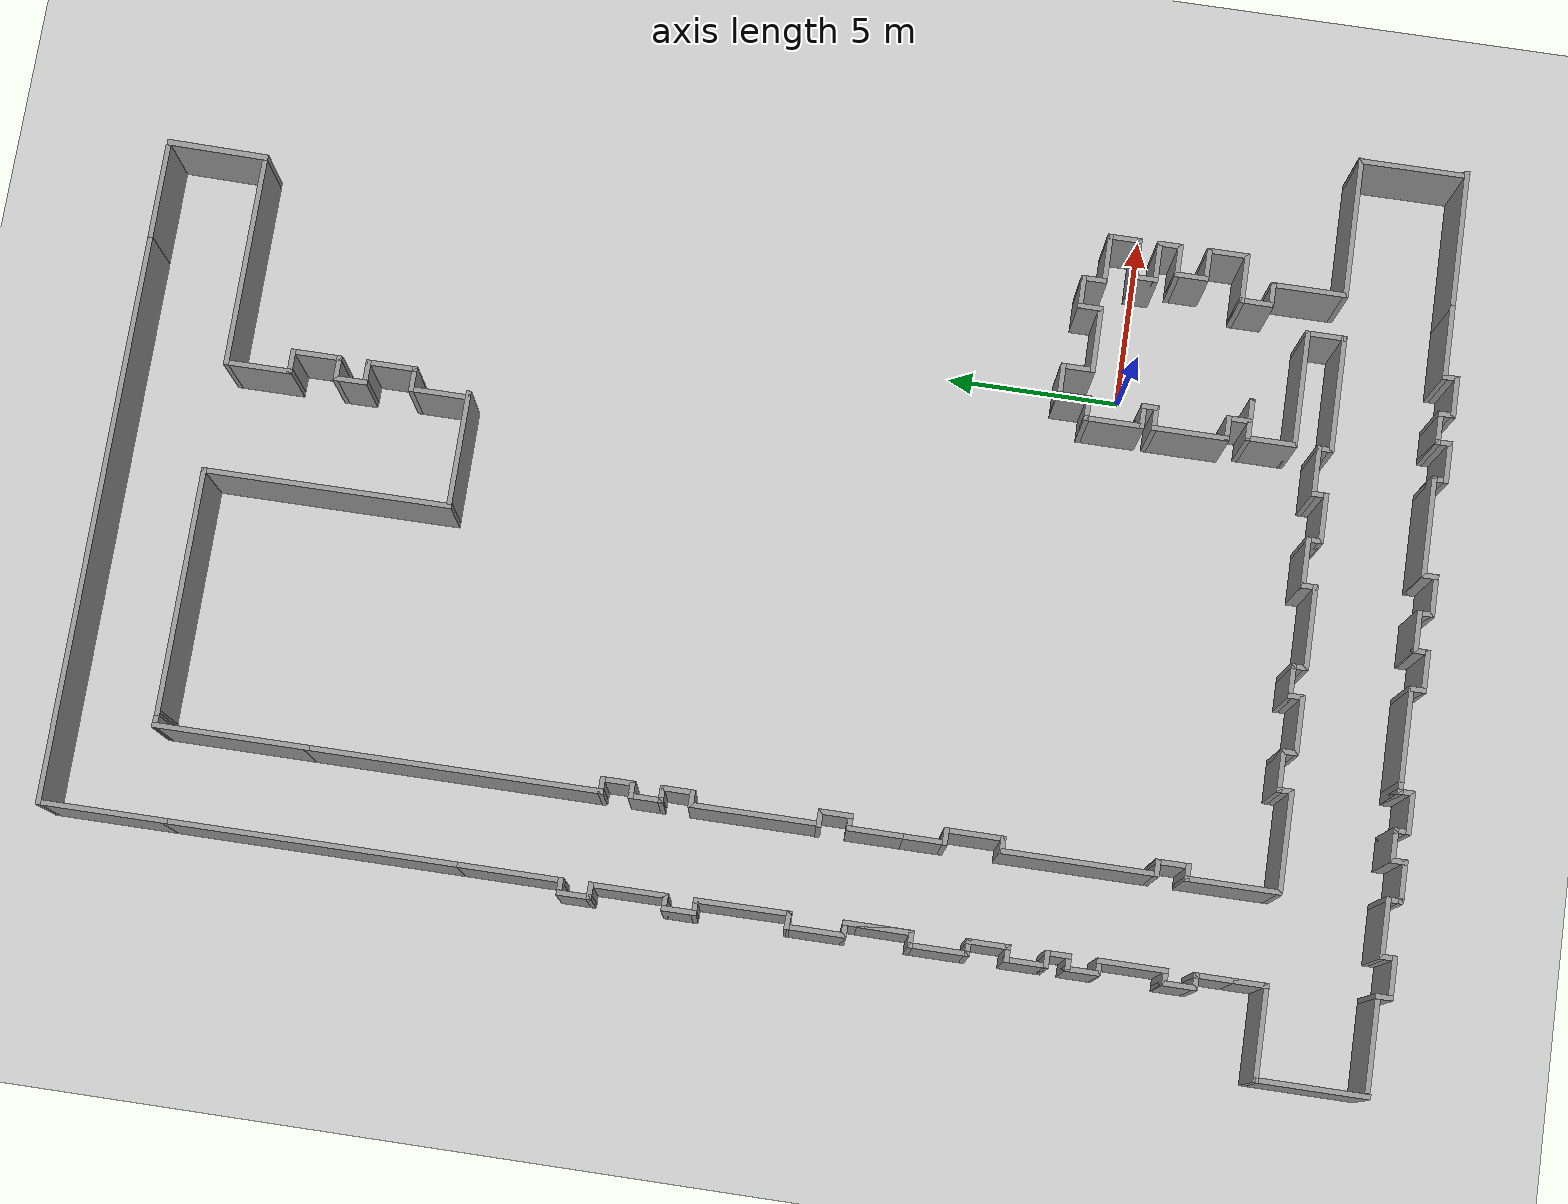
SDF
<sdf version="1.7">
 <world name="default">
  <light name="sun" type="directional">
   <pose>0 0 10 0 -0 0</pose>
   <diffuse>0.8 0.8 0.8 1</diffuse>
   <specular>0.2 0.2 0.2 1</specular>
   <attenuation>
    <range>1000</range>
    <constant>0.9</constant>
    <linear>0.01</linear>
    <quadratic>0.001</quadratic>
   </attenuation>
   <direction>-0.5 0.1 -0.9</direction>
   <spot><inner_angle>0</inner_angle><outer_angle>0</outer_angle><falloff>0</falloff></spot>
  </light>
  <model name="ground_plane">
   <static>1</static>
   <link name="link">
    <collision name="collision">
     <geometry><plane><normal>0 0 1</normal><size>1 1</size></plane></geometry>
     <surface><friction><ode><mu>100</mu><mu2>50</mu2></ode></friction></surface>
    </collision>
    <visual name="visual">
     <cast_shadows>0</cast_shadows>
     <geometry><plane><normal>0 0 1</normal><size>1 1</size></plane></geometry>
     <material>
      <script><uri>file://media/materials/scripts/gazebo.material</uri><name>Gazebo/Grey</name></script>
     </material>
    </visual>
   </link>
  </model>
  <gravity>0 0 -9.8</gravity>
  <magnetic_field>6e-06 2.3e-05 -4.2e-05</magnetic_field>
  <atmosphere type="adiabatic"/>
  <physics name="default_physics" default="0" type="ode">
   <max_step_size>0.001</max_step_size>
   <real_time_factor>1</real_time_factor>
   <real_time_update_rate>1000</real_time_update_rate>
  </physics>
  <scene><ambient>0.4 0.4 0.4 1</ambient><background>0.7 0.7 0.7 1</background><shadows>1</shadows></scene>
  <audio><device>default</device></audio>
  <spherical_coordinates>
   <surface_model>EARTH_WGS84</surface_model>
   <latitude_deg>0</latitude_deg>
   <longitude_deg>0</longitude_deg>
   <elevation>0</elevation>
   <heading_deg>0</heading_deg>
  </spherical_coordinates>
  <model name="HRI_1">
   <pose>-5.72111 9.59502 0 0 -0 0</pose>
   <link name="Wall_0">
    <collision name="Wall_0_Collision">
     <geometry><box><size>0.75 0.15 2.5</size></box></geometry>
     <pose>0 0 1.25 0 -0 0</pose>
    </collision>
    <visual name="Wall_0_Visual">
     <pose>0 0 1.25 0 -0 0</pose>
     <geometry><box><size>0.75 0.15 2.5</size></box></geometry>
     <material>
      <script><uri>file://media/materials/scripts/gazebo.material</uri><name>Gazebo/Grey</name></script>
      <ambient>1 1 1 1</ambient>
     </material>
     <meta><layer>0</layer></meta>
    </visual>
    <pose>4.79204 -8.57985 0 0 -0 3.14159</pose>
   </link>
   <link name="Wall_1">
    <collision name="Wall_1_Collision">
     <geometry><box><size>1.75 0.15 2.5</size></box></geometry>
     <pose>0 0 1.25 0 -0 0</pose>
    </collision>
    <visual name="Wall_1_Visual">
     <pose>0 0 1.25 0 -0 0</pose>
     <geometry><box><size>1.75 0.15 2.5</size></box></geometry>
     <material>
      <script><uri>file://media/materials/scripts/gazebo.material</uri><name>Gazebo/Grey</name></script>
      <ambient>1 1 1 1</ambient>
     </material>
     <meta><layer>0</layer></meta>
    </visual>
    <pose>4.49204 -9.37985 0 0 -0 -1.5708</pose>
   </link>
   <link name="Wall_10">
    <collision name="Wall_10_Collision">
     <geometry><box><size>1.5 0.15 2.5</size></box></geometry>
     <pose>0 0 1.25 0 -0 0</pose>
    </collision>
    <visual name="Wall_10_Visual">
     <pose>0 0 1.25 0 -0 0</pose>
     <geometry><box><size>1.5 0.15 2.5</size></box></geometry>
     <material>
      <script><uri>file://media/materials/scripts/gazebo.material</uri><name>Gazebo/Grey</name></script>
      <ambient>1 1 1 1</ambient>
     </material>
     <meta><layer>0</layer></meta>
    </visual>
    <pose>4.59204 -13.9049 0 0 -0 -1.5708</pose>
   </link>
   <link name="Wall_100">
    <collision name="Wall_100_Collision">
     <geometry><box><size>2 0.15 2.5</size></box></geometry>
     <pose>0 0 1.25 0 -0 0</pose>
    </collision>
    <visual name="Wall_100_Visual">
     <pose>0 0 1.25 0 -0 0</pose>
     <geometry><box><size>2 0.15 2.5</size></box></geometry>
     <material>
      <script><uri>file://media/materials/scripts/gazebo.material</uri><name>Gazebo/Grey</name></script>
      <ambient>1 1 1 1</ambient>
     </material>
     <meta><layer>0</layer></meta>
    </visual>
    <pose>-10.8271 -11.8378 0 0 -0 1.5708</pose>
   </link>
   <link name="Wall_101">
    <collision name="Wall_101_Collision">
     <geometry><box><size>0.5 0.15 2.5</size></box></geometry>
     <pose>0 0 1.25 0 -0 0</pose>
    </collision>
    <visual name="Wall_101_Visual">
     <pose>0 0 1.25 0 -0 0</pose>
     <geometry><box><size>0.5 0.15 2.5</size></box></geometry>
     <material>
      <script><uri>file://media/materials/scripts/gazebo.material</uri><name>Gazebo/Grey</name></script>
      <ambient>1 1 1 1</ambient>
     </material>
     <meta><layer>0</layer></meta>
    </visual>
    <pose>-11.0021 -10.9128 0 0 -0 3.14159</pose>
   </link>
   <link name="Wall_102">
    <collision name="Wall_102_Collision">
     <geometry><box><size>1 0.15 2.5</size></box></geometry>
     <pose>0 0 1.25 0 -0 0</pose>
    </collision>
    <visual name="Wall_102_Visual">
     <pose>0 0 1.25 0 -0 0</pose>
     <geometry><box><size>1 0.15 2.5</size></box></geometry>
     <material>
      <script><uri>file://media/materials/scripts/gazebo.material</uri><name>Gazebo/Grey</name></script>
      <ambient>1 1 1 1</ambient>
     </material>
     <meta><layer>0</layer></meta>
    </visual>
    <pose>-11.1771 -10.4878 0 0 -0 1.5708</pose>
   </link>
   <link name="Wall_103">
    <collision name="Wall_103_Collision">
     <geometry><box><size>0.5 0.15 2.5</size></box></geometry>
     <pose>0 0 1.25 0 -0 0</pose>
    </collision>
    <visual name="Wall_103_Visual">
     <pose>0 0 1.25 0 -0 0</pose>
     <geometry><box><size>0.5 0.15 2.5</size></box></geometry>
     <material>
      <script><uri>file://media/materials/scripts/gazebo.material</uri><name>Gazebo/Grey</name></script>
      <ambient>1 1 1 1</ambient>
     </material>
     <meta><layer>0</layer></meta>
    </visual>
    <pose>-11.0021 -10.0628 0 0 -0 0</pose>
   </link>
   <link name="Wall_108">
    <collision name="Wall_108_Collision">
     <geometry><box><size>0.5 0.15 2.5</size></box></geometry>
     <pose>0 0 1.25 0 -0 0</pose>
    </collision>
    <visual name="Wall_108_Visual">
     <pose>0 0 1.25 0 -0 0</pose>
     <geometry><box><size>0.5 0.15 2.5</size></box></geometry>
     <material>
      <script><uri>file://media/materials/scripts/gazebo.material</uri><name>Gazebo/Grey</name></script>
      <ambient>1 1 1 1</ambient>
     </material>
     <meta><layer>0</layer></meta>
    </visual>
    <pose>-11.0021 -8.36282 0 0 -0 0</pose>
   </link>
   <link name="Wall_11">
    <collision name="Wall_11_Collision">
     <geometry><box><size>3.5 0.15 2.5</size></box></geometry>
     <pose>0 0 1.25 0 -0 0</pose>
    </collision>
    <visual name="Wall_11_Visual">
     <pose>0 0 1.25 0 -0 0</pose>
     <geometry><box><size>3.5 0.15 2.5</size></box></geometry>
     <material>
      <script><uri>file://media/materials/scripts/gazebo.material</uri><name>Gazebo/Grey</name></script>
      <ambient>1 1 1 1</ambient>
     </material>
     <meta><layer>0</layer></meta>
    </visual>
    <pose>6.26704 -14.5799 0 0 -0 0</pose>
   </link>
   <link name="Wall_110">
    <collision name="Wall_110_Collision">
     <geometry><box><size>1.25 0.15 2.5</size></box></geometry>
     <pose>0 0 1.25 0 -0 0</pose>
    </collision>
    <visual name="Wall_110_Visual">
     <pose>0 0 1.25 0 -0 0</pose>
     <geometry><box><size>1.25 0.15 2.5</size></box></geometry>
     <material>
      <script><uri>file://media/materials/scripts/gazebo.material</uri><name>Gazebo/Grey</name></script>
      <ambient>1 1 1 1</ambient>
     </material>
     <meta><layer>0</layer></meta>
    </visual>
    <pose>-10.8271 -7.81282 0 0 -0 1.5708</pose>
   </link>
   <link name="Wall_111">
    <collision name="Wall_111_Collision">
     <geometry><box><size>0.5 0.15 2.5</size></box></geometry>
     <pose>0 0 1.25 0 -0 0</pose>
    </collision>
    <visual name="Wall_111_Visual">
     <pose>0 0 1.25 0 -0 0</pose>
     <geometry><box><size>0.5 0.15 2.5</size></box></geometry>
     <material>
      <script><uri>file://media/materials/scripts/gazebo.material</uri><name>Gazebo/Grey</name></script>
      <ambient>1 1 1 1</ambient>
     </material>
     <meta><layer>0</layer></meta>
    </visual>
    <pose>-11.0021 -7.26282 0 0 -0 3.14159</pose>
   </link>
   <link name="Wall_112">
    <collision name="Wall_112_Collision">
     <geometry><box><size>1.75 0.15 2.5</size></box></geometry>
     <pose>0 0 1.25 0 -0 0</pose>
    </collision>
    <visual name="Wall_112_Visual">
     <pose>0 0 1.25 0 -0 0</pose>
     <geometry><box><size>1.75 0.15 2.5</size></box></geometry>
     <material>
      <script><uri>file://media/materials/scripts/gazebo.material</uri><name>Gazebo/Grey</name></script>
      <ambient>1 1 1 1</ambient>
     </material>
     <meta><layer>0</layer></meta>
    </visual>
    <pose>-11.1771 -6.46282 0 0 -0 1.5708</pose>
   </link>
   <link name="Wall_113">
    <collision name="Wall_113_Collision">
     <geometry><box><size>0.495497 0.15 2.5</size></box></geometry>
     <pose>0 0 1.25 0 -0 0</pose>
    </collision>
    <visual name="Wall_113_Visual">
     <pose>0 0 1.25 0 -0 0</pose>
     <geometry><box><size>0.495497 0.15 2.5</size></box></geometry>
     <material>
      <script><uri>file://media/materials/scripts/gazebo.material</uri><name>Gazebo/Grey</name></script>
      <ambient>1 1 1 1</ambient>
     </material>
     <meta><layer>0</layer></meta>
    </visual>
    <pose>-11.0044 -5.66282 0 0 -0 0</pose>
   </link>
   <link name="Wall_117">
    <collision name="Wall_117_Collision">
     <geometry><box><size>2 0.15 2.5</size></box></geometry>
     <pose>0 0 1.25 0 -0 0</pose>
    </collision>
    <visual name="Wall_117_Visual">
     <pose>0 0 1.25 0 -0 0</pose>
     <geometry><box><size>2 0.15 2.5</size></box></geometry>
     <material>
      <script><uri>file://media/materials/scripts/gazebo.material</uri><name>Gazebo/Grey</name></script>
      <ambient>1 1 1 1</ambient>
     </material>
     <meta><layer>0</layer></meta>
    </visual>
    <pose>-10.8294 -4.73782 0 0 -0 1.56836</pose>
   </link>
   <link name="Wall_118">
    <collision name="Wall_118_Collision">
     <geometry><box><size>0.5 0.15 2.5</size></box></geometry>
     <pose>0 0 1.25 0 -0 0</pose>
    </collision>
    <visual name="Wall_118_Visual">
     <pose>0 0 1.25 0 -0 0</pose>
     <geometry><box><size>0.5 0.15 2.5</size></box></geometry>
     <material>
      <script><uri>file://media/materials/scripts/gazebo.material</uri><name>Gazebo/Grey</name></script>
      <ambient>1 1 1 1</ambient>
     </material>
     <meta><layer>0</layer></meta>
    </visual>
    <pose>-11.0021 -3.81282 0 0 -0 3.14159</pose>
   </link>
   <link name="Wall_119">
    <collision name="Wall_119_Collision">
     <geometry><box><size>1.75 0.15 2.5</size></box></geometry>
     <pose>0 0 1.25 0 -0 0</pose>
    </collision>
    <visual name="Wall_119_Visual">
     <pose>0 0 1.25 0 -0 0</pose>
     <geometry><box><size>1.75 0.15 2.5</size></box></geometry>
     <material>
      <script><uri>file://media/materials/scripts/gazebo.material</uri><name>Gazebo/Grey</name></script>
      <ambient>1 1 1 1</ambient>
     </material>
     <meta><layer>0</layer></meta>
    </visual>
    <pose>-11.1771 -3.01282 0 0 -0 1.5708</pose>
   </link>
   <link name="Wall_12">
    <collision name="Wall_12_Collision">
     <geometry><box><size>1.1925 0.15 2.5</size></box></geometry>
     <pose>0 0 1.25 0 -0 0</pose>
    </collision>
    <visual name="Wall_12_Visual">
     <pose>0 0 1.25 0 -0 0</pose>
     <geometry><box><size>1.1925 0.15 2.5</size></box></geometry>
     <material>
      <script><uri>file://media/materials/scripts/gazebo.material</uri><name>Gazebo/Grey</name></script>
      <ambient>1 1 1 1</ambient>
     </material>
     <meta><layer>0</layer></meta>
    </visual>
    <pose>7.94204 -15.1011 0 0 -0 -1.5708</pose>
   </link>
   <link name="Wall_120">
    <collision name="Wall_120_Collision">
     <geometry><box><size>0.517803 0.15 2.5</size></box></geometry>
     <pose>0 0 1.25 0 -0 0</pose>
    </collision>
    <visual name="Wall_120_Visual">
     <pose>0 0 1.25 0 -0 0</pose>
     <geometry><box><size>0.517803 0.15 2.5</size></box></geometry>
     <material>
      <script><uri>file://media/materials/scripts/gazebo.material</uri><name>Gazebo/Grey</name></script>
      <ambient>1 1 1 1</ambient>
     </material>
     <meta><layer>0</layer></meta>
    </visual>
    <pose>-10.9934 -2.22151 0 0 -0 -0.047302</pose>
   </link>
   <link name="Wall_123">
    <collision name="Wall_123_Collision">
     <geometry><box><size>0.5 0.15 2.5</size></box></geometry>
     <pose>0 0 1.25 0 -0 0</pose>
    </collision>
    <visual name="Wall_123_Visual">
     <pose>0 0 1.25 0 -0 0</pose>
     <geometry><box><size>0.5 0.15 2.5</size></box></geometry>
     <material>
      <script><uri>file://media/materials/scripts/gazebo.material</uri><name>Gazebo/Grey</name></script>
      <ambient>1 1 1 1</ambient>
     </material>
     <meta><layer>0</layer></meta>
    </visual>
    <pose>-11.0021 0.387183 0 0 -0 3.14159</pose>
   </link>
   <link name="Wall_124">
    <collision name="Wall_124_Collision">
     <geometry><box><size>1 0.15 2.5</size></box></geometry>
     <pose>0 0 1.25 0 -0 0</pose>
    </collision>
    <visual name="Wall_124_Visual">
     <pose>0 0 1.25 0 -0 0</pose>
     <geometry><box><size>1 0.15 2.5</size></box></geometry>
     <material>
      <script><uri>file://media/materials/scripts/gazebo.material</uri><name>Gazebo/Grey</name></script>
      <ambient>1 1 1 1</ambient>
     </material>
     <meta><layer>0</layer></meta>
    </visual>
    <pose>-11.1771 0.812183 0 0 -0 1.5708</pose>
   </link>
   <link name="Wall_125">
    <collision name="Wall_125_Collision">
     <geometry><box><size>0.5 0.15 2.5</size></box></geometry>
     <pose>0 0 1.25 0 -0 0</pose>
    </collision>
    <visual name="Wall_125_Visual">
     <pose>0 0 1.25 0 -0 0</pose>
     <geometry><box><size>0.5 0.15 2.5</size></box></geometry>
     <material>
      <script><uri>file://media/materials/scripts/gazebo.material</uri><name>Gazebo/Grey</name></script>
      <ambient>1 1 1 1</ambient>
     </material>
     <meta><layer>0</layer></meta>
    </visual>
    <pose>-11.0021 1.23718 0 0 -0 0</pose>
   </link>
   <link name="Wall_126">
    <collision name="Wall_126_Collision">
     <geometry><box><size>2.25 0.15 2.5</size></box></geometry>
     <pose>0 0 1.25 0 -0 0</pose>
    </collision>
    <visual name="Wall_126_Visual">
     <pose>0 0 1.25 0 -0 0</pose>
     <geometry><box><size>2.25 0.15 2.5</size></box></geometry>
     <material>
      <script><uri>file://media/materials/scripts/gazebo.material</uri><name>Gazebo/Grey</name></script>
      <ambient>1 1 1 1</ambient>
     </material>
     <meta><layer>0</layer></meta>
    </visual>
    <pose>-10.8271 2.28718 0 0 -0 1.5708</pose>
   </link>
   <link name="Wall_127">
    <collision name="Wall_127_Collision">
     <geometry><box><size>0.5 0.15 2.5</size></box></geometry>
     <pose>0 0 1.25 0 -0 0</pose>
    </collision>
    <visual name="Wall_127_Visual">
     <pose>0 0 1.25 0 -0 0</pose>
     <geometry><box><size>0.5 0.15 2.5</size></box></geometry>
     <material>
      <script><uri>file://media/materials/scripts/gazebo.material</uri><name>Gazebo/Grey</name></script>
      <ambient>1 1 1 1</ambient>
     </material>
     <meta><layer>0</layer></meta>
    </visual>
    <pose>-11.0021 3.33718 0 0 -0 3.14159</pose>
   </link>
   <link name="Wall_129">
    <collision name="Wall_129_Collision">
     <geometry><box><size>1 0.15 2.5</size></box></geometry>
     <pose>0 0 1.25 0 -0 0</pose>
    </collision>
    <visual name="Wall_129_Visual">
     <pose>0 0 1.25 0 -0 0</pose>
     <geometry><box><size>1 0.15 2.5</size></box></geometry>
     <material>
      <script><uri>file://media/materials/scripts/gazebo.material</uri><name>Gazebo/Grey</name></script>
      <ambient>1 1 1 1</ambient>
     </material>
     <meta><layer>0</layer></meta>
    </visual>
    <pose>-11.1771 3.76218 0 0 -0 1.5708</pose>
   </link>
   <link name="Wall_130">
    <collision name="Wall_130_Collision">
     <geometry><box><size>0.5 0.15 2.5</size></box></geometry>
     <pose>0 0 1.25 0 -0 0</pose>
    </collision>
    <visual name="Wall_130_Visual">
     <pose>0 0 1.25 0 -0 0</pose>
     <geometry><box><size>0.5 0.15 2.5</size></box></geometry>
     <material>
      <script><uri>file://media/materials/scripts/gazebo.material</uri><name>Gazebo/Grey</name></script>
      <ambient>1 1 1 1</ambient>
     </material>
     <meta><layer>0</layer></meta>
    </visual>
    <pose>-11.0021 4.18718 0 0 -0 0</pose>
   </link>
   <link name="Wall_131">
    <collision name="Wall_131_Collision">
     <geometry><box><size>3 0.15 2.5</size></box></geometry>
     <pose>0 0 1.25 0 -0 0</pose>
    </collision>
    <visual name="Wall_131_Visual">
     <pose>0 0 1.25 0 -0 0</pose>
     <geometry><box><size>3 0.15 2.5</size></box></geometry>
     <material>
      <script><uri>file://media/materials/scripts/gazebo.material</uri><name>Gazebo/Grey</name></script>
      <ambient>1 1 1 1</ambient>
     </material>
     <meta><layer>0</layer></meta>
    </visual>
    <pose>-10.8271 5.61218 0 0 -0 1.5708</pose>
   </link>
   <link name="Wall_133">
    <collision name="Wall_133_Collision">
     <geometry><box><size>2.75 0.15 2.5</size></box></geometry>
     <pose>0 0 1.25 0 -0 0</pose>
    </collision>
    <visual name="Wall_133_Visual">
     <pose>0 0 1.25 0 -0 0</pose>
     <geometry><box><size>2.75 0.15 2.5</size></box></geometry>
     <material>
      <script><uri>file://media/materials/scripts/gazebo.material</uri><name>Gazebo/Grey</name></script>
      <ambient>1 1 1 1</ambient>
     </material>
     <meta><layer>0</layer></meta>
    </visual>
    <pose>-8.20796 -14.3339 0 0 -0 1.5708</pose>
   </link>
   <link name="Wall_134">
    <collision name="Wall_134_Collision">
     <geometry><box><size>0.5 0.15 2.5</size></box></geometry>
     <pose>0 0 1.25 0 -0 0</pose>
    </collision>
    <visual name="Wall_134_Visual">
     <pose>0 0 1.25 0 -0 0</pose>
     <geometry><box><size>0.5 0.15 2.5</size></box></geometry>
     <material>
      <script><uri>file://media/materials/scripts/gazebo.material</uri><name>Gazebo/Grey</name></script>
      <ambient>1 1 1 1</ambient>
     </material>
     <meta><layer>0</layer></meta>
    </visual>
    <pose>-8.03296 -13.0339 0 0 -0 0</pose>
   </link>
   <link name="Wall_135">
    <collision name="Wall_135_Collision">
     <geometry><box><size>1 0.15 2.5</size></box></geometry>
     <pose>0 0 1.25 0 -0 0</pose>
    </collision>
    <visual name="Wall_135_Visual">
     <pose>0 0 1.25 0 -0 0</pose>
     <geometry><box><size>1 0.15 2.5</size></box></geometry>
     <material>
      <script><uri>file://media/materials/scripts/gazebo.material</uri><name>Gazebo/Grey</name></script>
      <ambient>1 1 1 1</ambient>
     </material>
     <meta><layer>0</layer></meta>
    </visual>
    <pose>-7.85796 -12.6089 0 0 -0 1.5708</pose>
   </link>
   <link name="Wall_136">
    <collision name="Wall_136_Collision">
     <geometry><box><size>0.5 0.15 2.5</size></box></geometry>
     <pose>0 0 1.25 0 -0 0</pose>
    </collision>
    <visual name="Wall_136_Visual">
     <pose>0 0 1.25 0 -0 0</pose>
     <geometry><box><size>0.5 0.15 2.5</size></box></geometry>
     <material>
      <script><uri>file://media/materials/scripts/gazebo.material</uri><name>Gazebo/Grey</name></script>
      <ambient>1 1 1 1</ambient>
     </material>
     <meta><layer>0</layer></meta>
    </visual>
    <pose>-8.03296 -12.1839 0 0 -0 3.14159</pose>
   </link>
   <link name="Wall_14">
    <collision name="Wall_14_Collision">
     <geometry><box><size>1 0.15 2.5</size></box></geometry>
     <pose>0 0 1.25 0 -0 0</pose>
    </collision>
    <visual name="Wall_14_Visual">
     <pose>0 0 1.25 0 -0 0</pose>
     <geometry><box><size>1 0.15 2.5</size></box></geometry>
     <material>
      <script><uri>file://media/materials/scripts/gazebo.material</uri><name>Gazebo/Grey</name></script>
      <ambient>1 1 1 1</ambient>
     </material>
     <meta><layer>0</layer></meta>
    </visual>
    <pose>5.09204 -8.15485 0 0 -0 1.5708</pose>
   </link>
   <link name="Wall_141">
    <collision name="Wall_141_Collision">
     <geometry><box><size>0.75 0.15 2.5</size></box></geometry>
     <pose>0 0 1.25 0 -0 0</pose>
    </collision>
    <visual name="Wall_141_Visual">
     <pose>0 0 1.25 0 -0 0</pose>
     <geometry><box><size>0.75 0.15 2.5</size></box></geometry>
     <material>
      <script><uri>file://media/materials/scripts/gazebo.material</uri><name>Gazebo/Grey</name></script>
      <ambient>1 1 1 1</ambient>
     </material>
     <meta><layer>0</layer></meta>
    </visual>
    <pose>-10.8271 -9.76282 0 0 -0 1.5708</pose>
   </link>
   <link name="Wall_142">
    <collision name="Wall_142_Collision">
     <geometry><box><size>0.5 0.15 2.5</size></box></geometry>
     <pose>0 0 1.25 0 -0 0</pose>
    </collision>
    <visual name="Wall_142_Visual">
     <pose>0 0 1.25 0 -0 0</pose>
     <geometry><box><size>0.5 0.15 2.5</size></box></geometry>
     <material>
      <script><uri>file://media/materials/scripts/gazebo.material</uri><name>Gazebo/Grey</name></script>
      <ambient>1 1 1 1</ambient>
     </material>
     <meta><layer>0</layer></meta>
    </visual>
    <pose>-11.0021 -9.46282 0 0 -0 3.14159</pose>
   </link>
   <link name="Wall_143">
    <collision name="Wall_143_Collision">
     <geometry><box><size>1.25 0.15 2.5</size></box></geometry>
     <pose>0 0 1.25 0 -0 0</pose>
    </collision>
    <visual name="Wall_143_Visual">
     <pose>0 0 1.25 0 -0 0</pose>
     <geometry><box><size>1.25 0.15 2.5</size></box></geometry>
     <material>
      <script><uri>file://media/materials/scripts/gazebo.material</uri><name>Gazebo/Grey</name></script>
      <ambient>1 1 1 1</ambient>
     </material>
     <meta><layer>0</layer></meta>
    </visual>
    <pose>-11.1771 -8.91282 0 0 -0 1.5708</pose>
   </link>
   <link name="Wall_146">
    <collision name="Wall_146_Collision">
     <geometry><box><size>4.5 0.15 2.5</size></box></geometry>
     <pose>0 0 1.25 0 -0 0</pose>
    </collision>
    <visual name="Wall_146_Visual">
     <pose>0 0 1.25 0 -0 0</pose>
     <geometry><box><size>4.5 0.15 2.5</size></box></geometry>
     <material>
      <script><uri>file://media/materials/scripts/gazebo.material</uri><name>Gazebo/Grey</name></script>
      <ambient>1 1 1 1</ambient>
     </material>
     <meta><layer>0</layer></meta>
    </visual>
    <pose>-8.20796 -10.0089 0 0 -0 1.5708</pose>
   </link>
   <link name="Wall_147">
    <collision name="Wall_147_Collision">
     <geometry><box><size>0.5 0.15 2.5</size></box></geometry>
     <pose>0 0 1.25 0 -0 0</pose>
    </collision>
    <visual name="Wall_147_Visual">
     <pose>0 0 1.25 0 -0 0</pose>
     <geometry><box><size>0.5 0.15 2.5</size></box></geometry>
     <material>
      <script><uri>file://media/materials/scripts/gazebo.material</uri><name>Gazebo/Grey</name></script>
      <ambient>1 1 1 1</ambient>
     </material>
     <meta><layer>0</layer></meta>
    </visual>
    <pose>-8.03296 -7.83385 0 0 -0 0</pose>
   </link>
   <link name="Wall_148">
    <collision name="Wall_148_Collision">
     <geometry><box><size>1.75 0.15 2.5</size></box></geometry>
     <pose>0 0 1.25 0 -0 0</pose>
    </collision>
    <visual name="Wall_148_Visual">
     <pose>0 0 1.25 0 -0 0</pose>
     <geometry><box><size>1.75 0.15 2.5</size></box></geometry>
     <material>
      <script><uri>file://media/materials/scripts/gazebo.material</uri><name>Gazebo/Grey</name></script>
      <ambient>1 1 1 1</ambient>
     </material>
     <meta><layer>0</layer></meta>
    </visual>
    <pose>-7.85796 -7.03385 0 0 -0 1.5708</pose>
   </link>
   <link name="Wall_149">
    <collision name="Wall_149_Collision">
     <geometry><box><size>0.5 0.15 2.5</size></box></geometry>
     <pose>0 0 1.25 0 -0 0</pose>
    </collision>
    <visual name="Wall_149_Visual">
     <pose>0 0 1.25 0 -0 0</pose>
     <geometry><box><size>0.5 0.15 2.5</size></box></geometry>
     <material>
      <script><uri>file://media/materials/scripts/gazebo.material</uri><name>Gazebo/Grey</name></script>
      <ambient>1 1 1 1</ambient>
     </material>
     <meta><layer>0</layer></meta>
    </visual>
    <pose>-8.03296 -6.23385 0 0 -0 3.14159</pose>
   </link>
   <link name="Wall_15">
    <collision name="Wall_15_Collision">
     <geometry><box><size>1 0.15 2.5</size></box></geometry>
     <pose>0 0 1.25 0 -0 0</pose>
    </collision>
    <visual name="Wall_15_Visual">
     <pose>0 0 1.25 0 -0 0</pose>
     <geometry><box><size>1 0.15 2.5</size></box></geometry>
     <material>
      <script><uri>file://media/materials/scripts/gazebo.material</uri><name>Gazebo/Grey</name></script>
      <ambient>1 1 1 1</ambient>
     </material>
     <meta><layer>0</layer></meta>
    </visual>
    <pose>5.51704 -7.72985 0 0 -0 0</pose>
   </link>
   <link name="Wall_150">
    <collision name="Wall_150_Collision">
     <geometry><box><size>1.25 0.15 2.5</size></box></geometry>
     <pose>0 0 1.25 0 -0 0</pose>
    </collision>
    <visual name="Wall_150_Visual">
     <pose>0 0 1.25 0 -0 0</pose>
     <geometry><box><size>1.25 0.15 2.5</size></box></geometry>
     <material>
      <script><uri>file://media/materials/scripts/gazebo.material</uri><name>Gazebo/Grey</name></script>
      <ambient>1 1 1 1</ambient>
     </material>
     <meta><layer>0</layer></meta>
    </visual>
    <pose>-8.20796 -5.68385 0 0 -0 1.5708</pose>
   </link>
   <link name="Wall_152">
    <collision name="Wall_152_Collision">
     <geometry><box><size>1.75 0.15 2.5</size></box></geometry>
     <pose>0 0 1.25 0 -0 0</pose>
    </collision>
    <visual name="Wall_152_Visual">
     <pose>0 0 1.25 0 -0 0</pose>
     <geometry><box><size>1.75 0.15 2.5</size></box></geometry>
     <material>
      <script><uri>file://media/materials/scripts/gazebo.material</uri><name>Gazebo/Grey</name></script>
      <ambient>1 1 1 1</ambient>
     </material>
     <meta><layer>0</layer></meta>
    </visual>
    <pose>-8.20796 -4.33385 0 0 -0 1.5708</pose>
   </link>
   <link name="Wall_16">
    <collision name="Wall_16_Collision">
     <geometry><box><size>1 0.15 2.5</size></box></geometry>
     <pose>0 0 1.25 0 -0 0</pose>
    </collision>
    <visual name="Wall_16_Visual">
     <pose>0 0 1.25 0 -0 0</pose>
     <geometry><box><size>1 0.15 2.5</size></box></geometry>
     <material>
      <script><uri>file://media/materials/scripts/gazebo.material</uri><name>Gazebo/Grey</name></script>
      <ambient>1 1 1 1</ambient>
     </material>
     <meta><layer>0</layer></meta>
    </visual>
    <pose>5.94204 -8.15485 0 0 -0 -1.5708</pose>
   </link>
   <link name="Wall_169">
    <collision name="Wall_169_Collision">
     <geometry><box><size>8.5 0.15 2.5</size></box></geometry>
     <pose>0 0 1.25 0 -0 0</pose>
    </collision>
    <visual name="Wall_169_Visual">
     <pose>0 0 1.25 0 -0 0</pose>
     <geometry><box><size>8.5 0.15 2.5</size></box></geometry>
     <material>
      <script><uri>file://media/materials/scripts/gazebo.material</uri><name>Gazebo/Grey</name></script>
      <ambient>1 1 1 1</ambient>
     </material>
     <meta><layer>0</layer></meta>
    </visual>
    <pose>-10.8271 11.2122 0 0 -0 1.5708</pose>
   </link>
   <link name="Wall_17">
    <collision name="Wall_17_Collision">
     <geometry><box><size>2 0.15 2.5</size></box></geometry>
     <pose>0 0 1.25 0 -0 0</pose>
    </collision>
    <visual name="Wall_17_Visual">
     <pose>0 0 1.25 0 -0 0</pose>
     <geometry><box><size>2 0.15 2.5</size></box></geometry>
     <material>
      <script><uri>file://media/materials/scripts/gazebo.material</uri><name>Gazebo/Grey</name></script>
      <ambient>1 1 1 1</ambient>
     </material>
     <meta><layer>0</layer></meta>
    </visual>
    <pose>6.86704 -8.57985 0 0 -0 0</pose>
   </link>
   <link name="Wall_171">
    <collision name="Wall_171_Collision">
     <geometry><box><size>3.75 0.15 2.5</size></box></geometry>
     <pose>0 0 1.25 0 -0 0</pose>
    </collision>
    <visual name="Wall_171_Visual">
     <pose>0 0 1.25 0 -0 0</pose>
     <geometry><box><size>3.75 0.15 2.5</size></box></geometry>
     <material>
      <script><uri>file://media/materials/scripts/gazebo.material</uri><name>Gazebo/Grey</name></script>
      <ambient>1 1 1 1</ambient>
     </material>
     <meta><layer>0</layer></meta>
    </visual>
    <pose>-10.8271 17.1872 0 0 -0 1.5708</pose>
   </link>
   <link name="Wall_173">
    <collision name="Wall_173_Collision">
     <geometry><box><size>16.75 0.15 2.5</size></box></geometry>
     <pose>0 0 1.25 0 -0 0</pose>
    </collision>
    <visual name="Wall_173_Visual">
     <pose>0 0 1.25 0 -0 0</pose>
     <geometry><box><size>16.75 0.15 2.5</size></box></geometry>
     <material>
      <script><uri>file://media/materials/scripts/gazebo.material</uri><name>Gazebo/Grey</name></script>
      <ambient>1 1 1 1</ambient>
     </material>
     <meta><layer>0</layer></meta>
    </visual>
    <pose>-2.52714 18.9872 0 0 -0 0</pose>
   </link>
   <link name="Wall_178">
    <collision name="Wall_178_Collision">
     <geometry><box><size>7.25 0.15 2.5</size></box></geometry>
     <pose>0 0 1.25 0 -0 0</pose>
    </collision>
    <visual name="Wall_178_Visual">
     <pose>0 0 1.25 0 -0 0</pose>
     <geometry><box><size>7.25 0.15 2.5</size></box></geometry>
     <material>
      <script><uri>file://media/materials/scripts/gazebo.material</uri><name>Gazebo/Grey</name></script>
      <ambient>1 1 1 1</ambient>
     </material>
     <meta><layer>0</layer></meta>
    </visual>
    <pose>-4.30796 16.1661 0 0 -0 0</pose>
   </link>
   <link name="Wall_18">
    <collision name="Wall_18_Collision">
     <geometry><box><size>0.75 0.15 2.5</size></box></geometry>
     <pose>0 0 1.25 0 -0 0</pose>
    </collision>
    <visual name="Wall_18_Visual">
     <pose>0 0 1.25 0 -0 0</pose>
     <geometry><box><size>0.75 0.15 2.5</size></box></geometry>
     <material>
      <script><uri>file://media/materials/scripts/gazebo.material</uri><name>Gazebo/Grey</name></script>
      <ambient>1 1 1 1</ambient>
     </material>
     <meta><layer>0</layer></meta>
    </visual>
    <pose>7.79204 -8.27985 0 0 -0 1.5708</pose>
   </link>
   <link name="Wall_180">
    <collision name="Wall_180_Collision">
     <geometry><box><size>7.25 0.15 2.5</size></box></geometry>
     <pose>0 0 1.25 0 -0 0</pose>
    </collision>
    <visual name="Wall_180_Visual">
     <pose>0 0 1.25 0 -0 0</pose>
     <geometry><box><size>7.25 0.15 2.5</size></box></geometry>
     <material>
      <script><uri>file://media/materials/scripts/gazebo.material</uri><name>Gazebo/Grey</name></script>
      <ambient>1 1 1 1</ambient>
     </material>
     <meta><layer>0</layer></meta>
    </visual>
    <pose>-0.757962 12.6161 0 0 -0 -1.5708</pose>
   </link>
   <link name="Wall_182">
    <collision name="Wall_182_Collision">
     <geometry><box><size>3.5 0.15 2.5</size></box></geometry>
     <pose>0 0 1.25 0 -0 0</pose>
    </collision>
    <visual name="Wall_182_Visual">
     <pose>0 0 1.25 0 -0 0</pose>
     <geometry><box><size>3.5 0.15 2.5</size></box></geometry>
     <material>
      <script><uri>file://media/materials/scripts/gazebo.material</uri><name>Gazebo/Grey</name></script>
      <ambient>1 1 1 1</ambient>
     </material>
     <meta><layer>0</layer></meta>
    </visual>
    <pose>0.917038 9.06615 0 0 -0 0</pose>
   </link>
   <link name="Wall_184">
    <collision name="Wall_184_Collision">
     <geometry><box><size>6.25 0.15 2.5</size></box></geometry>
     <pose>0 0 1.25 0 -0 0</pose>
    </collision>
    <visual name="Wall_184_Visual">
     <pose>0 0 1.25 0 -0 0</pose>
     <geometry><box><size>6.25 0.15 2.5</size></box></geometry>
     <material>
      <script><uri>file://media/materials/scripts/gazebo.material</uri><name>Gazebo/Grey</name></script>
      <ambient>1 1 1 1</ambient>
     </material>
     <meta><layer>0</layer></meta>
    </visual>
    <pose>5.5273 16.1174 0 0 -0 0</pose>
   </link>
   <link name="Wall_186">
    <collision name="Wall_186_Collision">
     <geometry><box><size>3 0.15 2.5</size></box></geometry>
     <pose>0 0 1.25 0 -0 0</pose>
    </collision>
    <visual name="Wall_186_Visual">
     <pose>0 0 1.25 0 -0 0</pose>
     <geometry><box><size>3 0.15 2.5</size></box></geometry>
     <material>
      <script><uri>file://media/materials/scripts/gazebo.material</uri><name>Gazebo/Grey</name></script>
      <ambient>1 1 1 1</ambient>
     </material>
     <meta><layer>0</layer></meta>
    </visual>
    <pose>7.19786 18.9872 0 0 -0 0</pose>
   </link>
   <link name="Wall_188">
    <collision name="Wall_188_Collision">
     <geometry><box><size>2 0.15 2.5</size></box></geometry>
     <pose>0 0 1.25 0 -0 0</pose>
    </collision>
    <visual name="Wall_188_Visual">
     <pose>0 0 1.25 0 -0 0</pose>
     <geometry><box><size>2 0.15 2.5</size></box></geometry>
     <material>
      <script><uri>file://media/materials/scripts/gazebo.material</uri><name>Gazebo/Grey</name></script>
      <ambient>1 1 1 1</ambient>
     </material>
     <meta><layer>0</layer></meta>
    </visual>
    <pose>2.4773 15.1924 0 0 -0 -1.5708</pose>
   </link>
   <link name="Wall_189">
    <collision name="Wall_189_Collision">
     <geometry><box><size>0.75 0.15 2.5</size></box></geometry>
     <pose>0 0 1.25 0 -0 0</pose>
    </collision>
    <visual name="Wall_189_Visual">
     <pose>0 0 1.25 0 -0 0</pose>
     <geometry><box><size>0.75 0.15 2.5</size></box></geometry>
     <material>
      <script><uri>file://media/materials/scripts/gazebo.material</uri><name>Gazebo/Grey</name></script>
      <ambient>1 1 1 1</ambient>
     </material>
     <meta><layer>0</layer></meta>
    </visual>
    <pose>2.7773 14.2674 0 0 -0 0</pose>
   </link>
   <link name="Wall_19">
    <collision name="Wall_19_Collision">
     <geometry><box><size>1 0.15 2.5</size></box></geometry>
     <pose>0 0 1.25 0 -0 0</pose>
    </collision>
    <visual name="Wall_19_Visual">
     <pose>0 0 1.25 0 -0 0</pose>
     <geometry><box><size>1 0.15 2.5</size></box></geometry>
     <material>
      <script><uri>file://media/materials/scripts/gazebo.material</uri><name>Gazebo/Grey</name></script>
      <ambient>1 1 1 1</ambient>
     </material>
     <meta><layer>0</layer></meta>
    </visual>
    <pose>8.21704 -7.97985 0 0 -0 0</pose>
   </link>
   <link name="Wall_190">
    <collision name="Wall_190_Collision">
     <geometry><box><size>1.5 0.15 2.5</size></box></geometry>
     <pose>0 0 1.25 0 -0 0</pose>
    </collision>
    <visual name="Wall_190_Visual">
     <pose>0 0 1.25 0 -0 0</pose>
     <geometry><box><size>1.5 0.15 2.5</size></box></geometry>
     <material>
      <script><uri>file://media/materials/scripts/gazebo.material</uri><name>Gazebo/Grey</name></script>
      <ambient>1 1 1 1</ambient>
     </material>
     <meta><layer>0</layer></meta>
    </visual>
    <pose>3.0773 13.5924 0 0 -0 -1.5708</pose>
   </link>
   <link name="Wall_191">
    <collision name="Wall_191_Collision">
     <geometry><box><size>0.75 0.15 2.5</size></box></geometry>
     <pose>0 0 1.25 0 -0 0</pose>
    </collision>
    <visual name="Wall_191_Visual">
     <pose>0 0 1.25 0 -0 0</pose>
     <geometry><box><size>0.75 0.15 2.5</size></box></geometry>
     <material>
      <script><uri>file://media/materials/scripts/gazebo.material</uri><name>Gazebo/Grey</name></script>
      <ambient>1 1 1 1</ambient>
     </material>
     <meta><layer>0</layer></meta>
    </visual>
    <pose>2.7773 12.9174 0 0 -0 3.14159</pose>
   </link>
   <link name="Wall_192">
    <collision name="Wall_192_Collision">
     <geometry><box><size>1 0.15 2.5</size></box></geometry>
     <pose>0 0 1.25 0 -0 0</pose>
    </collision>
    <visual name="Wall_192_Visual">
     <pose>0 0 1.25 0 -0 0</pose>
     <geometry><box><size>1 0.15 2.5</size></box></geometry>
     <material>
      <script><uri>file://media/materials/scripts/gazebo.material</uri><name>Gazebo/Grey</name></script>
      <ambient>1 1 1 1</ambient>
     </material>
     <meta><layer>0</layer></meta>
    </visual>
    <pose>2.4773 12.4924 0 0 -0 -1.5708</pose>
   </link>
   <link name="Wall_193">
    <collision name="Wall_193_Collision">
     <geometry><box><size>0.75 0.15 2.5</size></box></geometry>
     <pose>0 0 1.25 0 -0 0</pose>
    </collision>
    <visual name="Wall_193_Visual">
     <pose>0 0 1.25 0 -0 0</pose>
     <geometry><box><size>0.75 0.15 2.5</size></box></geometry>
     <material>
      <script><uri>file://media/materials/scripts/gazebo.material</uri><name>Gazebo/Grey</name></script>
      <ambient>1 1 1 1</ambient>
     </material>
     <meta><layer>0</layer></meta>
    </visual>
    <pose>2.7773 12.0674 0 0 -0 0</pose>
   </link>
   <link name="Wall_194">
    <collision name="Wall_194_Collision">
     <geometry><box><size>1.5 0.15 2.5</size></box></geometry>
     <pose>0 0 1.25 0 -0 0</pose>
    </collision>
    <visual name="Wall_194_Visual">
     <pose>0 0 1.25 0 -0 0</pose>
     <geometry><box><size>1.5 0.15 2.5</size></box></geometry>
     <material>
      <script><uri>file://media/materials/scripts/gazebo.material</uri><name>Gazebo/Grey</name></script>
      <ambient>1 1 1 1</ambient>
     </material>
     <meta><layer>0</layer></meta>
    </visual>
    <pose>3.0773 11.3924 0 0 -0 -1.5708</pose>
   </link>
   <link name="Wall_195">
    <collision name="Wall_195_Collision">
     <geometry><box><size>0.75 0.15 2.5</size></box></geometry>
     <pose>0 0 1.25 0 -0 0</pose>
    </collision>
    <visual name="Wall_195_Visual">
     <pose>0 0 1.25 0 -0 0</pose>
     <geometry><box><size>0.75 0.15 2.5</size></box></geometry>
     <material>
      <script><uri>file://media/materials/scripts/gazebo.material</uri><name>Gazebo/Grey</name></script>
      <ambient>1 1 1 1</ambient>
     </material>
     <meta><layer>0</layer></meta>
    </visual>
    <pose>2.7773 10.7174 0 0 -0 3.14159</pose>
   </link>
   <link name="Wall_196">
    <collision name="Wall_196_Collision">
     <geometry><box><size>1.75 0.15 2.5</size></box></geometry>
     <pose>0 0 1.25 0 -0 0</pose>
    </collision>
    <visual name="Wall_196_Visual">
     <pose>0 0 1.25 0 -0 0</pose>
     <geometry><box><size>1.75 0.15 2.5</size></box></geometry>
     <material>
      <script><uri>file://media/materials/scripts/gazebo.material</uri><name>Gazebo/Grey</name></script>
      <ambient>1 1 1 1</ambient>
     </material>
     <meta><layer>0</layer></meta>
    </visual>
    <pose>2.4773 9.91743 0 0 -0 -1.5708</pose>
   </link>
   <link name="Wall_198">
    <collision name="Wall_198_Collision">
     <geometry><box><size>2.75 0.15 2.5</size></box></geometry>
     <pose>0 0 1.25 0 -0 0</pose>
    </collision>
    <visual name="Wall_198_Visual">
     <pose>0 0 1.25 0 -0 0</pose>
     <geometry><box><size>2.75 0.15 2.5</size></box></geometry>
     <material>
      <script><uri>file://media/materials/scripts/gazebo.material</uri><name>Gazebo/Grey</name></script>
      <ambient>1 1 1 1</ambient>
     </material>
     <meta><layer>0</layer></meta>
    </visual>
    <pose>-12.1271 -15.5628 0 0 -0 3.14159</pose>
   </link>
   <link name="Wall_199">
    <collision name="Wall_199_Collision">
     <geometry><box><size>3.25 0.15 2.5</size></box></geometry>
     <pose>0 0 1.25 0 -0 0</pose>
    </collision>
    <visual name="Wall_199_Visual">
     <pose>0 0 1.25 0 -0 0</pose>
     <geometry><box><size>3.25 0.15 2.5</size></box></geometry>
     <material>
      <script><uri>file://media/materials/scripts/gazebo.material</uri><name>Gazebo/Grey</name></script>
      <ambient>1 1 1 1</ambient>
     </material>
     <meta><layer>0</layer></meta>
    </visual>
    <pose>-13.4271 -17.1128 0 0 -0 -1.5708</pose>
   </link>
   <link name="Wall_2">
    <collision name="Wall_2_Collision">
     <geometry><box><size>0.75 0.15 2.5</size></box></geometry>
     <pose>0 0 1.25 0 -0 0</pose>
    </collision>
    <visual name="Wall_2_Visual">
     <pose>0 0 1.25 0 -0 0</pose>
     <geometry><box><size>0.75 0.15 2.5</size></box></geometry>
     <material>
      <script><uri>file://media/materials/scripts/gazebo.material</uri><name>Gazebo/Grey</name></script>
      <ambient>1 1 1 1</ambient>
     </material>
     <meta><layer>0</layer></meta>
    </visual>
    <pose>4.79204 -10.1799 0 0 -0 0</pose>
   </link>
   <link name="Wall_20">
    <collision name="Wall_20_Collision">
     <geometry><box><size>0.75 0.15 2.5</size></box></geometry>
     <pose>0 0 1.25 0 -0 0</pose>
    </collision>
    <visual name="Wall_20_Visual">
     <pose>0 0 1.25 0 -0 0</pose>
     <geometry><box><size>0.75 0.15 2.5</size></box></geometry>
     <material>
      <script><uri>file://media/materials/scripts/gazebo.material</uri><name>Gazebo/Grey</name></script>
      <ambient>1 1 1 1</ambient>
     </material>
     <meta><layer>0</layer></meta>
    </visual>
    <pose>8.64204 -8.27985 0 0 -0 -1.5708</pose>
   </link>
   <link name="Wall_203">
    <collision name="Wall_203_Collision">
     <geometry><box><size>1.60288 0.15 2.5</size></box></geometry>
     <pose>0 0 1.25 0 -0 0</pose>
    </collision>
    <visual name="Wall_203_Visual">
     <pose>0 0 1.25 0 -0 0</pose>
     <geometry><box><size>1.60288 0.15 2.5</size></box></geometry>
     <material>
      <script><uri>file://media/materials/scripts/gazebo.material</uri><name>Gazebo/Grey</name></script>
      <ambient>1 1 1 1</ambient>
     </material>
     <meta><layer>0</layer></meta>
    </visual>
    <pose>-10.8358 -4.93639 0 0 -0 -1.57702</pose>
   </link>
   <link name="Wall_205">
    <collision name="Wall_205_Collision">
     <geometry><box><size>2.76745 0.15 2.5</size></box></geometry>
     <pose>0 0 1.25 0 -0 0</pose>
    </collision>
    <visual name="Wall_205_Visual">
     <pose>0 0 1.25 0 -0 0</pose>
     <geometry><box><size>2.76745 0.15 2.5</size></box></geometry>
     <material>
      <script><uri>file://media/materials/scripts/gazebo.material</uri><name>Gazebo/Grey</name></script>
      <ambient>1 1 1 1</ambient>
     </material>
     <meta><layer>0</layer></meta>
    </visual>
    <pose>-10.8184 -0.921513 0 0 -0 -1.56415</pose>
   </link>
   <link name="Wall_21">
    <collision name="Wall_21_Collision">
     <geometry><box><size>1.5 0.15 2.5</size></box></geometry>
     <pose>0 0 1.25 0 -0 0</pose>
    </collision>
    <visual name="Wall_21_Visual">
     <pose>0 0 1.25 0 -0 0</pose>
     <geometry><box><size>1.5 0.15 2.5</size></box></geometry>
     <material>
      <script><uri>file://media/materials/scripts/gazebo.material</uri><name>Gazebo/Grey</name></script>
      <ambient>1 1 1 1</ambient>
     </material>
     <meta><layer>0</layer></meta>
    </visual>
    <pose>9.31704 -8.57985 0 0 -0 0</pose>
   </link>
   <link name="Wall_211">
    <collision name="Wall_211_Collision">
     <geometry><box><size>0.5 0.15 2.5</size></box></geometry>
     <pose>0 0 1.25 0 -0 0</pose>
    </collision>
    <visual name="Wall_211_Visual">
     <pose>0 0 1.25 0 -0 0</pose>
     <geometry><box><size>0.5 0.15 2.5</size></box></geometry>
     <material>
      <script><uri>file://media/materials/scripts/gazebo.material</uri><name>Gazebo/Grey</name></script>
      <ambient>1 1 1 1</ambient>
     </material>
     <meta><layer>0</layer></meta>
    </visual>
    <pose>-8.03296 -3.53385 0 0 -0 0</pose>
   </link>
   <link name="Wall_212">
    <collision name="Wall_212_Collision">
     <geometry><box><size>1 0.15 2.5</size></box></geometry>
     <pose>0 0 1.25 0 -0 0</pose>
    </collision>
    <visual name="Wall_212_Visual">
     <pose>0 0 1.25 0 -0 0</pose>
     <geometry><box><size>1 0.15 2.5</size></box></geometry>
     <material>
      <script><uri>file://media/materials/scripts/gazebo.material</uri><name>Gazebo/Grey</name></script>
      <ambient>1 1 1 1</ambient>
     </material>
     <meta><layer>0</layer></meta>
    </visual>
    <pose>-7.85796 -3.10885 0 0 -0 1.5708</pose>
   </link>
   <link name="Wall_213">
    <collision name="Wall_213_Collision">
     <geometry><box><size>0.51749 0.15 2.5</size></box></geometry>
     <pose>0 0 1.25 0 -0 0</pose>
    </collision>
    <visual name="Wall_213_Visual">
     <pose>0 0 1.25 0 -0 0</pose>
     <geometry><box><size>0.51749 0.15 2.5</size></box></geometry>
     <material>
      <script><uri>file://media/materials/scripts/gazebo.material</uri><name>Gazebo/Grey</name></script>
      <ambient>1 1 1 1</ambient>
     </material>
     <meta><layer>0</layer></meta>
    </visual>
    <pose>-8.04171 -2.68385 0 0 -0 3.14159</pose>
   </link>
   <link name="Wall_215">
    <collision name="Wall_215_Collision">
     <geometry><box><size>3.75 0.15 2.5</size></box></geometry>
     <pose>0 0 1.25 0 -0 0</pose>
    </collision>
    <visual name="Wall_215_Visual">
     <pose>0 0 1.25 0 -0 0</pose>
     <geometry><box><size>3.75 0.15 2.5</size></box></geometry>
     <material>
      <script><uri>file://media/materials/scripts/gazebo.material</uri><name>Gazebo/Grey</name></script>
      <ambient>1 1 1 1</ambient>
     </material>
     <meta><layer>0</layer></meta>
    </visual>
    <pose>-8.20796 -0.866363 0 0 -0 1.5708</pose>
   </link>
   <link name="Wall_217">
    <collision name="Wall_217_Collision">
     <geometry><box><size>0.5 0.15 2.5</size></box></geometry>
     <pose>0 0 1.25 0 -0 0</pose>
    </collision>
    <visual name="Wall_217_Visual">
     <pose>0 0 1.25 0 -0 0</pose>
     <geometry><box><size>0.5 0.15 2.5</size></box></geometry>
     <material>
      <script><uri>file://media/materials/scripts/gazebo.material</uri><name>Gazebo/Grey</name></script>
      <ambient>1 1 1 1</ambient>
     </material>
     <meta><layer>0</layer></meta>
    </visual>
    <pose>-8.03296 0.933637 0 0 -0 0</pose>
   </link>
   <link name="Wall_218">
    <collision name="Wall_218_Collision">
     <geometry><box><size>1 0.15 2.5</size></box></geometry>
     <pose>0 0 1.25 0 -0 0</pose>
    </collision>
    <visual name="Wall_218_Visual">
     <pose>0 0 1.25 0 -0 0</pose>
     <geometry><box><size>1 0.15 2.5</size></box></geometry>
     <material>
      <script><uri>file://media/materials/scripts/gazebo.material</uri><name>Gazebo/Grey</name></script>
      <ambient>1 1 1 1</ambient>
     </material>
     <meta><layer>0</layer></meta>
    </visual>
    <pose>-7.85796 1.35864 0 0 -0 1.5708</pose>
   </link>
   <link name="Wall_219">
    <collision name="Wall_219_Collision">
     <geometry><box><size>0.5 0.15 2.5</size></box></geometry>
     <pose>0 0 1.25 0 -0 0</pose>
    </collision>
    <visual name="Wall_219_Visual">
     <pose>0 0 1.25 0 -0 0</pose>
     <geometry><box><size>0.5 0.15 2.5</size></box></geometry>
     <material>
      <script><uri>file://media/materials/scripts/gazebo.material</uri><name>Gazebo/Grey</name></script>
      <ambient>1 1 1 1</ambient>
     </material>
     <meta><layer>0</layer></meta>
    </visual>
    <pose>-8.03296 1.78364 0 0 -0 3.14159</pose>
   </link>
   <link name="Wall_22">
    <collision name="Wall_22_Collision">
     <geometry><box><size>1 0.15 2.5</size></box></geometry>
     <pose>0 0 1.25 0 -0 0</pose>
    </collision>
    <visual name="Wall_22_Visual">
     <pose>0 0 1.25 0 -0 0</pose>
     <geometry><box><size>1 0.15 2.5</size></box></geometry>
     <material>
      <script><uri>file://media/materials/scripts/gazebo.material</uri><name>Gazebo/Grey</name></script>
      <ambient>1 1 1 1</ambient>
     </material>
     <meta><layer>0</layer></meta>
    </visual>
    <pose>9.99204 -9.00485 0 0 -0 -1.5708</pose>
   </link>
   <link name="Wall_220">
    <collision name="Wall_220_Collision">
     <geometry><box><size>1 0.15 2.5</size></box></geometry>
     <pose>0 0 1.25 0 -0 0</pose>
    </collision>
    <visual name="Wall_220_Visual">
     <pose>0 0 1.25 0 -0 0</pose>
     <geometry><box><size>1 0.15 2.5</size></box></geometry>
     <material>
      <script><uri>file://media/materials/scripts/gazebo.material</uri><name>Gazebo/Grey</name></script>
      <ambient>1 1 1 1</ambient>
     </material>
     <meta><layer>0</layer></meta>
    </visual>
    <pose>-8.20796 2.20864 0 0 -0 1.5708</pose>
   </link>
   <link name="Wall_221">
    <collision name="Wall_221_Collision">
     <geometry><box><size>0.5 0.15 2.5</size></box></geometry>
     <pose>0 0 1.25 0 -0 0</pose>
    </collision>
    <visual name="Wall_221_Visual">
     <pose>0 0 1.25 0 -0 0</pose>
     <geometry><box><size>0.5 0.15 2.5</size></box></geometry>
     <material>
      <script><uri>file://media/materials/scripts/gazebo.material</uri><name>Gazebo/Grey</name></script>
      <ambient>1 1 1 1</ambient>
     </material>
     <meta><layer>0</layer></meta>
    </visual>
    <pose>-8.03296 2.63364 0 0 -0 0</pose>
   </link>
   <link name="Wall_222">
    <collision name="Wall_222_Collision">
     <geometry><box><size>1 0.15 2.5</size></box></geometry>
     <pose>0 0 1.25 0 -0 0</pose>
    </collision>
    <visual name="Wall_222_Visual">
     <pose>0 0 1.25 0 -0 0</pose>
     <geometry><box><size>1 0.15 2.5</size></box></geometry>
     <material>
      <script><uri>file://media/materials/scripts/gazebo.material</uri><name>Gazebo/Grey</name></script>
      <ambient>1 1 1 1</ambient>
     </material>
     <meta><layer>0</layer></meta>
    </visual>
    <pose>-7.85796 3.05864 0 0 -0 1.5708</pose>
   </link>
   <link name="Wall_223">
    <collision name="Wall_223_Collision">
     <geometry><box><size>0.5 0.15 2.5</size></box></geometry>
     <pose>0 0 1.25 0 -0 0</pose>
    </collision>
    <visual name="Wall_223_Visual">
     <pose>0 0 1.25 0 -0 0</pose>
     <geometry><box><size>0.5 0.15 2.5</size></box></geometry>
     <material>
      <script><uri>file://media/materials/scripts/gazebo.material</uri><name>Gazebo/Grey</name></script>
      <ambient>1 1 1 1</ambient>
     </material>
     <meta><layer>0</layer></meta>
    </visual>
    <pose>-8.03296 3.48364 0 0 -0 3.14159</pose>
   </link>
   <link name="Wall_225">
    <collision name="Wall_225_Collision">
     <geometry><box><size>8.5 0.15 2.5</size></box></geometry>
     <pose>0 0 1.25 0 -0 0</pose>
    </collision>
    <visual name="Wall_225_Visual">
     <pose>0 0 1.25 0 -0 0</pose>
     <geometry><box><size>8.5 0.15 2.5</size></box></geometry>
     <material>
      <script><uri>file://media/materials/scripts/gazebo.material</uri><name>Gazebo/Grey</name></script>
      <ambient>1 1 1 1</ambient>
     </material>
     <meta><layer>0</layer></meta>
    </visual>
    <pose>-8.20796 7.65864 0 0 -0 1.5708</pose>
   </link>
   <link name="Wall_227">
    <collision name="Wall_227_Collision">
     <geometry><box><size>4.5 0.15 2.5</size></box></geometry>
     <pose>0 0 1.25 0 -0 0</pose>
    </collision>
    <visual name="Wall_227_Visual">
     <pose>0 0 1.25 0 -0 0</pose>
     <geometry><box><size>4.5 0.15 2.5</size></box></geometry>
     <material>
      <script><uri>file://media/materials/scripts/gazebo.material</uri><name>Gazebo/Grey</name></script>
      <ambient>1 1 1 1</ambient>
     </material>
     <meta><layer>0</layer></meta>
    </visual>
    <pose>-8.20796 14.0086 0 0 -0 1.5708</pose>
   </link>
   <link name="Wall_229">
    <collision name="Wall_229_Collision">
     <geometry><box><size>0.500437 0.15 2.5</size></box></geometry>
     <pose>0 0 1.25 0 -0 0</pose>
    </collision>
    <visual name="Wall_229_Visual">
     <pose>0 0 1.25 0 -0 0</pose>
     <geometry><box><size>0.500437 0.15 2.5</size></box></geometry>
     <material>
      <script><uri>file://media/materials/scripts/gazebo.material</uri><name>Gazebo/Grey</name></script>
      <ambient>1 1 1 1</ambient>
     </material>
     <meta><layer>0</layer></meta>
    </visual>
    <pose>-8.03296 16.1749 0 0 -0 3.09166</pose>
   </link>
   <link name="Wall_23">
    <collision name="Wall_23_Collision">
     <geometry><box><size>1.25 0.15 2.5</size></box></geometry>
     <pose>0 0 1.25 0 -0 0</pose>
    </collision>
    <visual name="Wall_23_Visual">
     <pose>0 0 1.25 0 -0 0</pose>
     <geometry><box><size>1.25 0.15 2.5</size></box></geometry>
     <material>
      <script><uri>file://media/materials/scripts/gazebo.material</uri><name>Gazebo/Grey</name></script>
      <ambient>1 1 1 1</ambient>
     </material>
     <meta><layer>0</layer></meta>
    </visual>
    <pose>9.44204 -9.42985 0 0 -0 3.14159</pose>
   </link>
   <link name="Wall_231">
    <collision name="Wall_231_Collision">
     <geometry><box><size>3.25 0.15 2.5</size></box></geometry>
     <pose>0 0 1.25 0 -0 0</pose>
    </collision>
    <visual name="Wall_231_Visual">
     <pose>0 0 1.25 0 -0 0</pose>
     <geometry><box><size>3.25 0.15 2.5</size></box></geometry>
     <material>
      <script><uri>file://media/materials/scripts/gazebo.material</uri><name>Gazebo/Grey</name></script>
      <ambient>1 1 1 1</ambient>
     </material>
     <meta><layer>0</layer></meta>
    </visual>
    <pose>13.3595 -17.0799 0 0 -0 -1.5708</pose>
   </link>
   <link name="Wall_24">
    <collision name="Wall_24_Collision">
     <geometry><box><size>0.75 0.15 2.5</size></box></geometry>
     <pose>0 0 1.25 0 -0 0</pose>
    </collision>
    <visual name="Wall_24_Visual">
     <pose>0 0 1.25 0 -0 0</pose>
     <geometry><box><size>0.75 0.15 2.5</size></box></geometry>
     <material>
      <script><uri>file://media/materials/scripts/gazebo.material</uri><name>Gazebo/Grey</name></script>
      <ambient>1 1 1 1</ambient>
     </material>
     <meta><layer>0</layer></meta>
    </visual>
    <pose>8.89204 -9.72985 0 0 -0 -1.5708</pose>
   </link>
   <link name="Wall_25">
    <collision name="Wall_25_Collision">
     <geometry><box><size>1.25 0.15 2.5</size></box></geometry>
     <pose>0 0 1.25 0 -0 0</pose>
    </collision>
    <visual name="Wall_25_Visual">
     <pose>0 0 1.25 0 -0 0</pose>
     <geometry><box><size>1.25 0.15 2.5</size></box></geometry>
     <material>
      <script><uri>file://media/materials/scripts/gazebo.material</uri><name>Gazebo/Grey</name></script>
      <ambient>1 1 1 1</ambient>
     </material>
     <meta><layer>0</layer></meta>
    </visual>
    <pose>9.44204 -10.0299 0 0 -0 0</pose>
   </link>
   <link name="Wall_26">
    <collision name="Wall_26_Collision">
     <geometry><box><size>0.75 0.15 2.5</size></box></geometry>
     <pose>0 0 1.25 0 -0 0</pose>
    </collision>
    <visual name="Wall_26_Visual">
     <pose>0 0 1.25 0 -0 0</pose>
     <geometry><box><size>0.75 0.15 2.5</size></box></geometry>
     <material>
      <script><uri>file://media/materials/scripts/gazebo.material</uri><name>Gazebo/Grey</name></script>
      <ambient>1 1 1 1</ambient>
     </material>
     <meta><layer>0</layer></meta>
    </visual>
    <pose>9.99204 -10.3299 0 0 -0 -1.5708</pose>
   </link>
   <link name="Wall_27">
    <collision name="Wall_27_Collision">
     <geometry><box><size>1 0.15 2.5</size></box></geometry>
     <pose>0 0 1.25 0 -0 0</pose>
    </collision>
    <visual name="Wall_27_Visual">
     <pose>0 0 1.25 0 -0 0</pose>
     <geometry><box><size>1 0.15 2.5</size></box></geometry>
     <material>
      <script><uri>file://media/materials/scripts/gazebo.material</uri><name>Gazebo/Grey</name></script>
      <ambient>1 1 1 1</ambient>
     </material>
     <meta><layer>0</layer></meta>
    </visual>
    <pose>9.56704 -10.6299 0 0 -0 3.14159</pose>
   </link>
   <link name="Wall_28">
    <collision name="Wall_28_Collision">
     <geometry><box><size>1 0.15 2.5</size></box></geometry>
     <pose>0 0 1.25 0 -0 0</pose>
    </collision>
    <visual name="Wall_28_Visual">
     <pose>0 0 1.25 0 -0 0</pose>
     <geometry><box><size>1 0.15 2.5</size></box></geometry>
     <material>
      <script><uri>file://media/materials/scripts/gazebo.material</uri><name>Gazebo/Grey</name></script>
      <ambient>1 1 1 1</ambient>
     </material>
     <meta><layer>0</layer></meta>
    </visual>
    <pose>9.14204 -11.0549 0 0 -0 -1.5708</pose>
   </link>
   <link name="Wall_29">
    <collision name="Wall_29_Collision">
     <geometry><box><size>1 0.15 2.5</size></box></geometry>
     <pose>0 0 1.25 0 -0 0</pose>
    </collision>
    <visual name="Wall_29_Visual">
     <pose>0 0 1.25 0 -0 0</pose>
     <geometry><box><size>1 0.15 2.5</size></box></geometry>
     <material>
      <script><uri>file://media/materials/scripts/gazebo.material</uri><name>Gazebo/Grey</name></script>
      <ambient>1 1 1 1</ambient>
     </material>
     <meta><layer>0</layer></meta>
    </visual>
    <pose>9.56704 -11.4799 0 0 -0 0</pose>
   </link>
   <link name="Wall_3">
    <collision name="Wall_3_Collision">
     <geometry><box><size>0.5 0.15 2.5</size></box></geometry>
     <pose>0 0 1.25 0 -0 0</pose>
    </collision>
    <visual name="Wall_3_Visual">
     <pose>0 0 1.25 0 -0 0</pose>
     <geometry><box><size>0.5 0.15 2.5</size></box></geometry>
     <material>
      <script><uri>file://media/materials/scripts/gazebo.material</uri><name>Gazebo/Grey</name></script>
      <ambient>1 1 1 1</ambient>
     </material>
     <meta><layer>0</layer></meta>
    </visual>
    <pose>5.09204 -10.3549 0 0 -0 -1.5708</pose>
   </link>
   <link name="Wall_30">
    <collision name="Wall_30_Collision">
     <geometry><box><size>1.25 0.15 2.5</size></box></geometry>
     <pose>0 0 1.25 0 -0 0</pose>
    </collision>
    <visual name="Wall_30_Visual">
     <pose>0 0 1.25 0 -0 0</pose>
     <geometry><box><size>1.25 0.15 2.5</size></box></geometry>
     <material>
      <script><uri>file://media/materials/scripts/gazebo.material</uri><name>Gazebo/Grey</name></script>
      <ambient>1 1 1 1</ambient>
     </material>
     <meta><layer>0</layer></meta>
    </visual>
    <pose>9.99204 -12.0299 0 0 -0 -1.5708</pose>
   </link>
   <link name="Wall_31">
    <collision name="Wall_31_Collision">
     <geometry><box><size>1.5 0.15 2.5</size></box></geometry>
     <pose>0 0 1.25 0 -0 0</pose>
    </collision>
    <visual name="Wall_31_Visual">
     <pose>0 0 1.25 0 -0 0</pose>
     <geometry><box><size>1.5 0.15 2.5</size></box></geometry>
     <material>
      <script><uri>file://media/materials/scripts/gazebo.material</uri><name>Gazebo/Grey</name></script>
      <ambient>1 1 1 1</ambient>
     </material>
     <meta><layer>0</layer></meta>
    </visual>
    <pose>9.31704 -12.5799 0 0 -0 3.14159</pose>
   </link>
   <link name="Wall_32">
    <collision name="Wall_32_Collision">
     <geometry><box><size>1 0.15 2.5</size></box></geometry>
     <pose>0 0 1.25 0 -0 0</pose>
    </collision>
    <visual name="Wall_32_Visual">
     <pose>0 0 1.25 0 -0 0</pose>
     <geometry><box><size>1 0.15 2.5</size></box></geometry>
     <material>
      <script><uri>file://media/materials/scripts/gazebo.material</uri><name>Gazebo/Grey</name></script>
      <ambient>1 1 1 1</ambient>
     </material>
     <meta><layer>0</layer></meta>
    </visual>
    <pose>8.64204 -13.0049 0 0 -0 -1.5708</pose>
   </link>
   <link name="Wall_33">
    <collision name="Wall_33_Collision">
     <geometry><box><size>0.75 0.15 2.5</size></box></geometry>
     <pose>0 0 1.25 0 -0 0</pose>
    </collision>
    <visual name="Wall_33_Visual">
     <pose>0 0 1.25 0 -0 0</pose>
     <geometry><box><size>0.75 0.15 2.5</size></box></geometry>
     <material>
      <script><uri>file://media/materials/scripts/gazebo.material</uri><name>Gazebo/Grey</name></script>
      <ambient>1 1 1 1</ambient>
     </material>
     <meta><layer>0</layer></meta>
    </visual>
    <pose>8.94204 -13.4299 0 0 -0 0</pose>
   </link>
   <link name="Wall_34">
    <collision name="Wall_34_Collision">
     <geometry><box><size>2.25 0.15 2.5</size></box></geometry>
     <pose>0 0 1.25 0 -0 0</pose>
    </collision>
    <visual name="Wall_34_Visual">
     <pose>0 0 1.25 0 -0 0</pose>
     <geometry><box><size>2.25 0.15 2.5</size></box></geometry>
     <material>
      <script><uri>file://media/materials/scripts/gazebo.material</uri><name>Gazebo/Grey</name></script>
      <ambient>1 1 1 1</ambient>
     </material>
     <meta><layer>0</layer></meta>
    </visual>
    <pose>9.24204 -14.4799 0 0 -0 -1.5708</pose>
   </link>
   <link name="Wall_35">
    <collision name="Wall_35_Collision">
     <geometry><box><size>4.28498 0.15 2.5</size></box></geometry>
     <pose>0 0 1.25 0 -0 0</pose>
    </collision>
    <visual name="Wall_35_Visual">
     <pose>0 0 1.25 0 -0 0</pose>
     <geometry><box><size>4.28498 0.15 2.5</size></box></geometry>
     <material>
      <script><uri>file://media/materials/scripts/gazebo.material</uri><name>Gazebo/Grey</name></script>
      <ambient>1 1 1 1</ambient>
     </material>
     <meta><layer>0</layer></meta>
    </visual>
    <pose>11.3095 -15.5299 0 0 -0 0</pose>
   </link>
   <link name="Wall_37">
    <collision name="Wall_37_Collision">
     <geometry><box><size>4.25 0.15 2.5</size></box></geometry>
     <pose>0 0 1.25 0 -0 0</pose>
    </collision>
    <visual name="Wall_37_Visual">
     <pose>0 0 1.25 0 -0 0</pose>
     <geometry><box><size>4.25 0.15 2.5</size></box></geometry>
     <material>
      <script><uri>file://media/materials/scripts/gazebo.material</uri><name>Gazebo/Grey</name></script>
      <ambient>1 1 1 1</ambient>
     </material>
     <meta><layer>0</layer></meta>
    </visual>
    <pose>11.3771 -18.622 0 0 -0 0</pose>
   </link>
   <link name="Wall_39">
    <collision name="Wall_39_Collision">
     <geometry><box><size>3.5 0.15 2.5</size></box></geometry>
     <pose>0 0 1.25 0 -0 0</pose>
    </collision>
    <visual name="Wall_39_Visual">
     <pose>0 0 1.25 0 -0 0</pose>
     <geometry><box><size>3.5 0.15 2.5</size></box></geometry>
     <material>
      <script><uri>file://media/materials/scripts/gazebo.material</uri><name>Gazebo/Grey</name></script>
      <ambient>1 1 1 1</ambient>
     </material>
     <meta><layer>0</layer></meta>
    </visual>
    <pose>6.26704 -15.6339 0 0 -0 3.14159</pose>
   </link>
   <link name="Wall_4">
    <collision name="Wall_4_Collision">
     <geometry><box><size>0.75 0.15 2.5</size></box></geometry>
     <pose>0 0 1.25 0 -0 0</pose>
    </collision>
    <visual name="Wall_4_Visual">
     <pose>0 0 1.25 0 -0 0</pose>
     <geometry><box><size>0.75 0.15 2.5</size></box></geometry>
     <material>
      <script><uri>file://media/materials/scripts/gazebo.material</uri><name>Gazebo/Grey</name></script>
      <ambient>1 1 1 1</ambient>
     </material>
     <meta><layer>0</layer></meta>
    </visual>
    <pose>4.79204 -10.5299 0 0 -0 3.14159</pose>
   </link>
   <link name="Wall_41">
    <collision name="Wall_41_Collision">
     <geometry><box><size>0.5 0.15 2.5</size></box></geometry>
     <pose>0 0 1.25 0 -0 0</pose>
    </collision>
    <visual name="Wall_41_Visual">
     <pose>0 0 1.25 0 -0 0</pose>
     <geometry><box><size>0.5 0.15 2.5</size></box></geometry>
     <material>
      <script><uri>file://media/materials/scripts/gazebo.material</uri><name>Gazebo/Grey</name></script>
      <ambient>1 1 1 1</ambient>
     </material>
     <meta><layer>0</layer></meta>
    </visual>
    <pose>4.59204 -15.4589 0 0 -0 1.5708</pose>
   </link>
   <link name="Wall_42">
    <collision name="Wall_42_Collision">
     <geometry><box><size>1.5 0.15 2.5</size></box></geometry>
     <pose>0 0 1.25 0 -0 0</pose>
    </collision>
    <visual name="Wall_42_Visual">
     <pose>0 0 1.25 0 -0 0</pose>
     <geometry><box><size>1.5 0.15 2.5</size></box></geometry>
     <material>
      <script><uri>file://media/materials/scripts/gazebo.material</uri><name>Gazebo/Grey</name></script>
      <ambient>1 1 1 1</ambient>
     </material>
     <meta><layer>0</layer></meta>
    </visual>
    <pose>3.91704 -15.2839 0 0 -0 3.14159</pose>
   </link>
   <link name="Wall_43">
    <collision name="Wall_43_Collision">
     <geometry><box><size>0.5 0.15 2.5</size></box></geometry>
     <pose>0 0 1.25 0 -0 0</pose>
    </collision>
    <visual name="Wall_43_Visual">
     <pose>0 0 1.25 0 -0 0</pose>
     <geometry><box><size>0.5 0.15 2.5</size></box></geometry>
     <material>
      <script><uri>file://media/materials/scripts/gazebo.material</uri><name>Gazebo/Grey</name></script>
      <ambient>1 1 1 1</ambient>
     </material>
     <meta><layer>0</layer></meta>
    </visual>
    <pose>3.24204 -15.4589 0 0 -0 -1.5708</pose>
   </link>
   <link name="Wall_44">
    <collision name="Wall_44_Collision">
     <geometry><box><size>1.5 0.15 2.5</size></box></geometry>
     <pose>0 0 1.25 0 -0 0</pose>
    </collision>
    <visual name="Wall_44_Visual">
     <pose>0 0 1.25 0 -0 0</pose>
     <geometry><box><size>1.5 0.15 2.5</size></box></geometry>
     <material>
      <script><uri>file://media/materials/scripts/gazebo.material</uri><name>Gazebo/Grey</name></script>
      <ambient>1 1 1 1</ambient>
     </material>
     <meta><layer>0</layer></meta>
    </visual>
    <pose>2.56704 -15.6339 0 0 -0 3.14159</pose>
   </link>
   <link name="Wall_45">
    <collision name="Wall_45_Collision">
     <geometry><box><size>0.5 0.15 2.5</size></box></geometry>
     <pose>0 0 1.25 0 -0 0</pose>
    </collision>
    <visual name="Wall_45_Visual">
     <pose>0 0 1.25 0 -0 0</pose>
     <geometry><box><size>0.5 0.15 2.5</size></box></geometry>
     <material>
      <script><uri>file://media/materials/scripts/gazebo.material</uri><name>Gazebo/Grey</name></script>
      <ambient>1 1 1 1</ambient>
     </material>
     <meta><layer>0</layer></meta>
    </visual>
    <pose>1.89204 -15.4589 0 0 -0 1.5708</pose>
   </link>
   <link name="Wall_46">
    <collision name="Wall_46_Collision">
     <geometry><box><size>1.5 0.15 2.5</size></box></geometry>
     <pose>0 0 1.25 0 -0 0</pose>
    </collision>
    <visual name="Wall_46_Visual">
     <pose>0 0 1.25 0 -0 0</pose>
     <geometry><box><size>1.5 0.15 2.5</size></box></geometry>
     <material>
      <script><uri>file://media/materials/scripts/gazebo.material</uri><name>Gazebo/Grey</name></script>
      <ambient>1 1 1 1</ambient>
     </material>
     <meta><layer>0</layer></meta>
    </visual>
    <pose>1.21704 -15.2839 0 0 -0 3.14159</pose>
   </link>
   <link name="Wall_47">
    <collision name="Wall_47_Collision">
     <geometry><box><size>0.5 0.15 2.5</size></box></geometry>
     <pose>0 0 1.25 0 -0 0</pose>
    </collision>
    <visual name="Wall_47_Visual">
     <pose>0 0 1.25 0 -0 0</pose>
     <geometry><box><size>0.5 0.15 2.5</size></box></geometry>
     <material>
      <script><uri>file://media/materials/scripts/gazebo.material</uri><name>Gazebo/Grey</name></script>
      <ambient>1 1 1 1</ambient>
     </material>
     <meta><layer>0</layer></meta>
    </visual>
    <pose>0.542038 -15.4589 0 0 -0 -1.5708</pose>
   </link>
   <link name="Wall_48">
    <collision name="Wall_48_Collision">
     <geometry><box><size>2.5 0.15 2.5</size></box></geometry>
     <pose>0 0 1.25 0 -0 0</pose>
    </collision>
    <visual name="Wall_48_Visual">
     <pose>0 0 1.25 0 -0 0</pose>
     <geometry><box><size>2.5 0.15 2.5</size></box></geometry>
     <material>
      <script><uri>file://media/materials/scripts/gazebo.material</uri><name>Gazebo/Grey</name></script>
      <ambient>1 1 1 1</ambient>
     </material>
     <meta><layer>0</layer></meta>
    </visual>
    <pose>-0.632962 -15.6339 0 0 -0 3.14159</pose>
   </link>
   <link name="Wall_49">
    <collision name="Wall_49_Collision">
     <geometry><box><size>0.5 0.15 2.5</size></box></geometry>
     <pose>0 0 1.25 0 -0 0</pose>
    </collision>
    <visual name="Wall_49_Visual">
     <pose>0 0 1.25 0 -0 0</pose>
     <geometry><box><size>0.5 0.15 2.5</size></box></geometry>
     <material>
      <script><uri>file://media/materials/scripts/gazebo.material</uri><name>Gazebo/Grey</name></script>
      <ambient>1 1 1 1</ambient>
     </material>
     <meta><layer>0</layer></meta>
    </visual>
    <pose>-1.80796 -15.4589 0 0 -0 1.5708</pose>
   </link>
   <link name="Wall_5">
    <collision name="Wall_5_Collision">
     <geometry><box><size>2.25 0.15 2.5</size></box></geometry>
     <pose>0 0 1.25 0 -0 0</pose>
    </collision>
    <visual name="Wall_5_Visual">
     <pose>0 0 1.25 0 -0 0</pose>
     <geometry><box><size>2.25 0.15 2.5</size></box></geometry>
     <material>
      <script><uri>file://media/materials/scripts/gazebo.material</uri><name>Gazebo/Grey</name></script>
      <ambient>1 1 1 1</ambient>
     </material>
     <meta><layer>0</layer></meta>
    </visual>
    <pose>4.49204 -11.5799 0 0 -0 -1.5708</pose>
   </link>
   <link name="Wall_50">
    <collision name="Wall_50_Collision">
     <geometry><box><size>1 0.15 2.5</size></box></geometry>
     <pose>0 0 1.25 0 -0 0</pose>
    </collision>
    <visual name="Wall_50_Visual">
     <pose>0 0 1.25 0 -0 0</pose>
     <geometry><box><size>1 0.15 2.5</size></box></geometry>
     <material>
      <script><uri>file://media/materials/scripts/gazebo.material</uri><name>Gazebo/Grey</name></script>
      <ambient>1 1 1 1</ambient>
     </material>
     <meta><layer>0</layer></meta>
    </visual>
    <pose>-2.23296 -15.2839 0 0 -0 3.14159</pose>
   </link>
   <link name="Wall_51">
    <collision name="Wall_51_Collision">
     <geometry><box><size>0.5 0.15 2.5</size></box></geometry>
     <pose>0 0 1.25 0 -0 0</pose>
    </collision>
    <visual name="Wall_51_Visual">
     <pose>0 0 1.25 0 -0 0</pose>
     <geometry><box><size>0.5 0.15 2.5</size></box></geometry>
     <material>
      <script><uri>file://media/materials/scripts/gazebo.material</uri><name>Gazebo/Grey</name></script>
      <ambient>1 1 1 1</ambient>
     </material>
     <meta><layer>0</layer></meta>
    </visual>
    <pose>-2.65796 -15.4589 0 0 -0 -1.5708</pose>
   </link>
   <link name="Wall_53">
    <collision name="Wall_53_Collision">
     <geometry><box><size>1.75 0.15 2.5</size></box></geometry>
     <pose>0 0 1.25 0 -0 0</pose>
    </collision>
    <visual name="Wall_53_Visual">
     <pose>0 0 1.25 0 -0 0</pose>
     <geometry><box><size>1.75 0.15 2.5</size></box></geometry>
     <material>
      <script><uri>file://media/materials/scripts/gazebo.material</uri><name>Gazebo/Grey</name></script>
      <ambient>1 1 1 1</ambient>
     </material>
     <meta><layer>0</layer></meta>
    </visual>
    <pose>-3.45796 -15.6339 0 0 -0 3.14159</pose>
   </link>
   <link name="Wall_54">
    <collision name="Wall_54_Collision">
     <geometry><box><size>0.5 0.15 2.5</size></box></geometry>
     <pose>0 0 1.25 0 -0 0</pose>
    </collision>
    <visual name="Wall_54_Visual">
     <pose>0 0 1.25 0 -0 0</pose>
     <geometry><box><size>0.5 0.15 2.5</size></box></geometry>
     <material>
      <script><uri>file://media/materials/scripts/gazebo.material</uri><name>Gazebo/Grey</name></script>
      <ambient>1 1 1 1</ambient>
     </material>
     <meta><layer>0</layer></meta>
    </visual>
    <pose>-4.25796 -15.4589 0 0 -0 1.5708</pose>
   </link>
   <link name="Wall_55">
    <collision name="Wall_55_Collision">
     <geometry><box><size>1.25 0.15 2.5</size></box></geometry>
     <pose>0 0 1.25 0 -0 0</pose>
    </collision>
    <visual name="Wall_55_Visual">
     <pose>0 0 1.25 0 -0 0</pose>
     <geometry><box><size>1.25 0.15 2.5</size></box></geometry>
     <material>
      <script><uri>file://media/materials/scripts/gazebo.material</uri><name>Gazebo/Grey</name></script>
      <ambient>1 1 1 1</ambient>
     </material>
     <meta><layer>0</layer></meta>
    </visual>
    <pose>-4.80796 -15.2839 0 0 -0 3.14159</pose>
   </link>
   <link name="Wall_56">
    <collision name="Wall_56_Collision">
     <geometry><box><size>0.5 0.15 2.5</size></box></geometry>
     <pose>0 0 1.25 0 -0 0</pose>
    </collision>
    <visual name="Wall_56_Visual">
     <pose>0 0 1.25 0 -0 0</pose>
     <geometry><box><size>0.5 0.15 2.5</size></box></geometry>
     <material>
      <script><uri>file://media/materials/scripts/gazebo.material</uri><name>Gazebo/Grey</name></script>
      <ambient>1 1 1 1</ambient>
     </material>
     <meta><layer>0</layer></meta>
    </visual>
    <pose>-5.35796 -15.4589 0 0 -0 -1.5708</pose>
   </link>
   <link name="Wall_57">
    <collision name="Wall_57_Collision">
     <geometry><box><size>3 0.15 2.5</size></box></geometry>
     <pose>0 0 1.25 0 -0 0</pose>
    </collision>
    <visual name="Wall_57_Visual">
     <pose>0 0 1.25 0 -0 0</pose>
     <geometry><box><size>3 0.15 2.5</size></box></geometry>
     <material>
      <script><uri>file://media/materials/scripts/gazebo.material</uri><name>Gazebo/Grey</name></script>
      <ambient>1 1 1 1</ambient>
     </material>
     <meta><layer>0</layer></meta>
    </visual>
    <pose>-6.78296 -15.6339 0 0 -0 3.14159</pose>
   </link>
   <link name="Wall_59">
    <collision name="Wall_59_Collision">
     <geometry><box><size>2.25 0.15 2.5</size></box></geometry>
     <pose>0 0 1.25 0 -0 0</pose>
    </collision>
    <visual name="Wall_59_Visual">
     <pose>0 0 1.25 0 -0 0</pose>
     <geometry><box><size>2.25 0.15 2.5</size></box></geometry>
     <material>
      <script><uri>file://media/materials/scripts/gazebo.material</uri><name>Gazebo/Grey</name></script>
      <ambient>1 1 1 1</ambient>
     </material>
     <meta><layer>0</layer></meta>
    </visual>
    <pose>8.27714 -18.622 0 0 -0 3.14159</pose>
   </link>
   <link name="Wall_6">
    <collision name="Wall_6_Collision">
     <geometry><box><size>0.75 0.15 2.5</size></box></geometry>
     <pose>0 0 1.25 0 -0 0</pose>
    </collision>
    <visual name="Wall_6_Visual">
     <pose>0 0 1.25 0 -0 0</pose>
     <geometry><box><size>0.75 0.15 2.5</size></box></geometry>
     <material>
      <script><uri>file://media/materials/scripts/gazebo.material</uri><name>Gazebo/Grey</name></script>
      <ambient>1 1 1 1</ambient>
     </material>
     <meta><layer>0</layer></meta>
    </visual>
    <pose>4.79204 -12.6299 0 0 -0 0</pose>
   </link>
   <link name="Wall_60">
    <collision name="Wall_60_Collision">
     <geometry><box><size>0.5 0.15 2.5</size></box></geometry>
     <pose>0 0 1.25 0 -0 0</pose>
    </collision>
    <visual name="Wall_60_Visual">
     <pose>0 0 1.25 0 -0 0</pose>
     <geometry><box><size>0.5 0.15 2.5</size></box></geometry>
     <material>
      <script><uri>file://media/materials/scripts/gazebo.material</uri><name>Gazebo/Grey</name></script>
      <ambient>1 1 1 1</ambient>
     </material>
     <meta><layer>0</layer></meta>
    </visual>
    <pose>7.22714 -18.797 0 0 -0 -1.5708</pose>
   </link>
   <link name="Wall_61">
    <collision name="Wall_61_Collision">
     <geometry><box><size>1.25 0.15 2.5</size></box></geometry>
     <pose>0 0 1.25 0 -0 0</pose>
    </collision>
    <visual name="Wall_61_Visual">
     <pose>0 0 1.25 0 -0 0</pose>
     <geometry><box><size>1.25 0.15 2.5</size></box></geometry>
     <material>
      <script><uri>file://media/materials/scripts/gazebo.material</uri><name>Gazebo/Grey</name></script>
      <ambient>1 1 1 1</ambient>
     </material>
     <meta><layer>0</layer></meta>
    </visual>
    <pose>6.67714 -18.972 0 0 -0 3.14159</pose>
   </link>
   <link name="Wall_62">
    <collision name="Wall_62_Collision">
     <geometry><box><size>0.5 0.15 2.5</size></box></geometry>
     <pose>0 0 1.25 0 -0 0</pose>
    </collision>
    <visual name="Wall_62_Visual">
     <pose>0 0 1.25 0 -0 0</pose>
     <geometry><box><size>0.5 0.15 2.5</size></box></geometry>
     <material>
      <script><uri>file://media/materials/scripts/gazebo.material</uri><name>Gazebo/Grey</name></script>
      <ambient>1 1 1 1</ambient>
     </material>
     <meta><layer>0</layer></meta>
    </visual>
    <pose>6.12714 -18.797 0 0 -0 1.5708</pose>
   </link>
   <link name="Wall_63">
    <collision name="Wall_63_Collision">
     <geometry><box><size>1 0.15 2.5</size></box></geometry>
     <pose>0 0 1.25 0 -0 0</pose>
    </collision>
    <visual name="Wall_63_Visual">
     <pose>0 0 1.25 0 -0 0</pose>
     <geometry><box><size>1 0.15 2.5</size></box></geometry>
     <material>
      <script><uri>file://media/materials/scripts/gazebo.material</uri><name>Gazebo/Grey</name></script>
      <ambient>1 1 1 1</ambient>
     </material>
     <meta><layer>0</layer></meta>
    </visual>
    <pose>5.70214 -18.622 0 0 -0 3.14159</pose>
   </link>
   <link name="Wall_64">
    <collision name="Wall_64_Collision">
     <geometry><box><size>0.5 0.15 2.5</size></box></geometry>
     <pose>0 0 1.25 0 -0 0</pose>
    </collision>
    <visual name="Wall_64_Visual">
     <pose>0 0 1.25 0 -0 0</pose>
     <geometry><box><size>0.5 0.15 2.5</size></box></geometry>
     <material>
      <script><uri>file://media/materials/scripts/gazebo.material</uri><name>Gazebo/Grey</name></script>
      <ambient>1 1 1 1</ambient>
     </material>
     <meta><layer>0</layer></meta>
    </visual>
    <pose>5.27714 -18.797 0 0 -0 -1.5708</pose>
   </link>
   <link name="Wall_65">
    <collision name="Wall_65_Collision">
     <geometry><box><size>1.25 0.15 2.5</size></box></geometry>
     <pose>0 0 1.25 0 -0 0</pose>
    </collision>
    <visual name="Wall_65_Visual">
     <pose>0 0 1.25 0 -0 0</pose>
     <geometry><box><size>1.25 0.15 2.5</size></box></geometry>
     <material>
      <script><uri>file://media/materials/scripts/gazebo.material</uri><name>Gazebo/Grey</name></script>
      <ambient>1 1 1 1</ambient>
     </material>
     <meta><layer>0</layer></meta>
    </visual>
    <pose>4.72714 -18.972 0 0 -0 3.14159</pose>
   </link>
   <link name="Wall_66">
    <collision name="Wall_66_Collision">
     <geometry><box><size>0.484791 0.15 2.5</size></box></geometry>
     <pose>0 0 1.25 0 -0 0</pose>
    </collision>
    <visual name="Wall_66_Visual">
     <pose>0 0 1.25 0 -0 0</pose>
     <geometry><box><size>0.484791 0.15 2.5</size></box></geometry>
     <material>
      <script><uri>file://media/materials/scripts/gazebo.material</uri><name>Gazebo/Grey</name></script>
      <ambient>1 1 1 1</ambient>
     </material>
     <meta><layer>0</layer></meta>
    </visual>
    <pose>4.17714 -18.8046 0 0 -0 1.5708</pose>
   </link>
   <link name="Wall_67">
    <collision name="Wall_67_Collision">
     <geometry><box><size>3 0.15 2.5</size></box></geometry>
     <pose>0 0 1.25 0 -0 0</pose>
    </collision>
    <visual name="Wall_67_Visual">
     <pose>0 0 1.25 0 -0 0</pose>
     <geometry><box><size>3 0.15 2.5</size></box></geometry>
     <material>
      <script><uri>file://media/materials/scripts/gazebo.material</uri><name>Gazebo/Grey</name></script>
      <ambient>1 1 1 1</ambient>
     </material>
     <meta><layer>0</layer></meta>
    </visual>
    <pose>2.76735 -18.6372 0 0 -0 3.14159</pose>
   </link>
   <link name="Wall_7">
    <collision name="Wall_7_Collision">
     <geometry><box><size>0.75 0.15 2.5</size></box></geometry>
     <pose>0 0 1.25 0 -0 0</pose>
    </collision>
    <visual name="Wall_7_Visual">
     <pose>0 0 1.25 0 -0 0</pose>
     <geometry><box><size>0.75 0.15 2.5</size></box></geometry>
     <material>
      <script><uri>file://media/materials/scripts/gazebo.material</uri><name>Gazebo/Grey</name></script>
      <ambient>1 1 1 1</ambient>
     </material>
     <meta><layer>0</layer></meta>
    </visual>
    <pose>5.09204 -12.9299 0 0 -0 -1.5708</pose>
   </link>
   <link name="Wall_71">
    <collision name="Wall_71_Collision">
     <geometry><box><size>0.5 0.15 2.5</size></box></geometry>
     <pose>0 0 1.25 0 -0 0</pose>
    </collision>
    <visual name="Wall_71_Visual">
     <pose>0 0 1.25 0 -0 0</pose>
     <geometry><box><size>0.5 0.15 2.5</size></box></geometry>
     <material>
      <script><uri>file://media/materials/scripts/gazebo.material</uri><name>Gazebo/Grey</name></script>
      <ambient>1 1 1 1</ambient>
     </material>
     <meta><layer>0</layer></meta>
    </visual>
    <pose>1.34235 -18.8122 0 0 -0 -1.5708</pose>
   </link>
   <link name="Wall_72">
    <collision name="Wall_72_Collision">
     <geometry><box><size>1.25 0.15 2.5</size></box></geometry>
     <pose>0 0 1.25 0 -0 0</pose>
    </collision>
    <visual name="Wall_72_Visual">
     <pose>0 0 1.25 0 -0 0</pose>
     <geometry><box><size>1.25 0.15 2.5</size></box></geometry>
     <material>
      <script><uri>file://media/materials/scripts/gazebo.material</uri><name>Gazebo/Grey</name></script>
      <ambient>1 1 1 1</ambient>
     </material>
     <meta><layer>0</layer></meta>
    </visual>
    <pose>0.792351 -18.9872 0 0 -0 3.14159</pose>
   </link>
   <link name="Wall_73">
    <collision name="Wall_73_Collision">
     <geometry><box><size>0.5 0.15 2.5</size></box></geometry>
     <pose>0 0 1.25 0 -0 0</pose>
    </collision>
    <visual name="Wall_73_Visual">
     <pose>0 0 1.25 0 -0 0</pose>
     <geometry><box><size>0.5 0.15 2.5</size></box></geometry>
     <material>
      <script><uri>file://media/materials/scripts/gazebo.material</uri><name>Gazebo/Grey</name></script>
      <ambient>1 1 1 1</ambient>
     </material>
     <meta><layer>0</layer></meta>
    </visual>
    <pose>0.242351 -18.8122 0 0 -0 1.5708</pose>
   </link>
   <link name="Wall_74">
    <collision name="Wall_74_Collision">
     <geometry><box><size>1.25 0.15 2.5</size></box></geometry>
     <pose>0 0 1.25 0 -0 0</pose>
    </collision>
    <visual name="Wall_74_Visual">
     <pose>0 0 1.25 0 -0 0</pose>
     <geometry><box><size>1.25 0.15 2.5</size></box></geometry>
     <material>
      <script><uri>file://media/materials/scripts/gazebo.material</uri><name>Gazebo/Grey</name></script>
      <ambient>1 1 1 1</ambient>
     </material>
     <meta><layer>0</layer></meta>
    </visual>
    <pose>-0.307649 -18.6372 0 0 -0 3.14159</pose>
   </link>
   <link name="Wall_75">
    <collision name="Wall_75_Collision">
     <geometry><box><size>0.5 0.15 2.5</size></box></geometry>
     <pose>0 0 1.25 0 -0 0</pose>
    </collision>
    <visual name="Wall_75_Visual">
     <pose>0 0 1.25 0 -0 0</pose>
     <geometry><box><size>0.5 0.15 2.5</size></box></geometry>
     <material>
      <script><uri>file://media/materials/scripts/gazebo.material</uri><name>Gazebo/Grey</name></script>
      <ambient>1 1 1 1</ambient>
     </material>
     <meta><layer>0</layer></meta>
    </visual>
    <pose>-0.857649 -18.8122 0 0 -0 -1.5708</pose>
   </link>
   <link name="Wall_76">
    <collision name="Wall_76_Collision">
     <geometry><box><size>1.25 0.15 2.5</size></box></geometry>
     <pose>0 0 1.25 0 -0 0</pose>
    </collision>
    <visual name="Wall_76_Visual">
     <pose>0 0 1.25 0 -0 0</pose>
     <geometry><box><size>1.25 0.15 2.5</size></box></geometry>
     <material>
      <script><uri>file://media/materials/scripts/gazebo.material</uri><name>Gazebo/Grey</name></script>
      <ambient>1 1 1 1</ambient>
     </material>
     <meta><layer>0</layer></meta>
    </visual>
    <pose>-1.40765 -18.9872 0 0 -0 3.14159</pose>
   </link>
   <link name="Wall_77">
    <collision name="Wall_77_Collision">
     <geometry><box><size>0.5 0.15 2.5</size></box></geometry>
     <pose>0 0 1.25 0 -0 0</pose>
    </collision>
    <visual name="Wall_77_Visual">
     <pose>0 0 1.25 0 -0 0</pose>
     <geometry><box><size>0.5 0.15 2.5</size></box></geometry>
     <material>
      <script><uri>file://media/materials/scripts/gazebo.material</uri><name>Gazebo/Grey</name></script>
      <ambient>1 1 1 1</ambient>
     </material>
     <meta><layer>0</layer></meta>
    </visual>
    <pose>-1.95765 -18.8122 0 0 -0 1.5708</pose>
   </link>
   <link name="Wall_78">
    <collision name="Wall_78_Collision">
     <geometry><box><size>2.75 0.15 2.5</size></box></geometry>
     <pose>0 0 1.25 0 -0 0</pose>
    </collision>
    <visual name="Wall_78_Visual">
     <pose>0 0 1.25 0 -0 0</pose>
     <geometry><box><size>2.75 0.15 2.5</size></box></geometry>
     <material>
      <script><uri>file://media/materials/scripts/gazebo.material</uri><name>Gazebo/Grey</name></script>
      <ambient>1 1 1 1</ambient>
     </material>
     <meta><layer>0</layer></meta>
    </visual>
    <pose>-3.25765 -18.6372 0 0 -0 3.14159</pose>
   </link>
   <link name="Wall_8">
    <collision name="Wall_8_Collision">
     <geometry><box><size>0.75 0.15 2.5</size></box></geometry>
     <pose>0 0 1.25 0 -0 0</pose>
    </collision>
    <visual name="Wall_8_Visual">
     <pose>0 0 1.25 0 -0 0</pose>
     <geometry><box><size>0.75 0.15 2.5</size></box></geometry>
     <material>
      <script><uri>file://media/materials/scripts/gazebo.material</uri><name>Gazebo/Grey</name></script>
      <ambient>1 1 1 1</ambient>
     </material>
     <meta><layer>0</layer></meta>
    </visual>
    <pose>5.39204 -13.2299 0 0 -0 0</pose>
   </link>
   <link name="Wall_80">
    <collision name="Wall_80_Collision">
     <geometry><box><size>0.5 0.15 2.5</size></box></geometry>
     <pose>0 0 1.25 0 -0 0</pose>
    </collision>
    <visual name="Wall_80_Visual">
     <pose>0 0 1.25 0 -0 0</pose>
     <geometry><box><size>0.5 0.15 2.5</size></box></geometry>
     <material>
      <script><uri>file://media/materials/scripts/gazebo.material</uri><name>Gazebo/Grey</name></script>
      <ambient>1 1 1 1</ambient>
     </material>
     <meta><layer>0</layer></meta>
    </visual>
    <pose>-4.73265 -18.6372 0 0 -0 3.14159</pose>
   </link>
   <link name="Wall_81">
    <collision name="Wall_81_Collision">
     <geometry><box><size>0.5 0.15 2.5</size></box></geometry>
     <pose>0 0 1.25 0 -0 0</pose>
    </collision>
    <visual name="Wall_81_Visual">
     <pose>0 0 1.25 0 -0 0</pose>
     <geometry><box><size>0.5 0.15 2.5</size></box></geometry>
     <material>
      <script><uri>file://media/materials/scripts/gazebo.material</uri><name>Gazebo/Grey</name></script>
      <ambient>1 1 1 1</ambient>
     </material>
     <meta><layer>0</layer></meta>
    </visual>
    <pose>-4.90765 -18.8122 0 0 -0 -1.5708</pose>
   </link>
   <link name="Wall_82">
    <collision name="Wall_82_Collision">
     <geometry><box><size>1.25 0.15 2.5</size></box></geometry>
     <pose>0 0 1.25 0 -0 0</pose>
    </collision>
    <visual name="Wall_82_Visual">
     <pose>0 0 1.25 0 -0 0</pose>
     <geometry><box><size>1.25 0.15 2.5</size></box></geometry>
     <material>
      <script><uri>file://media/materials/scripts/gazebo.material</uri><name>Gazebo/Grey</name></script>
      <ambient>1 1 1 1</ambient>
     </material>
     <meta><layer>0</layer></meta>
    </visual>
    <pose>-5.45765 -18.9872 0 0 -0 3.14159</pose>
   </link>
   <link name="Wall_83">
    <collision name="Wall_83_Collision">
     <geometry><box><size>0.5 0.15 2.5</size></box></geometry>
     <pose>0 0 1.25 0 -0 0</pose>
    </collision>
    <visual name="Wall_83_Visual">
     <pose>0 0 1.25 0 -0 0</pose>
     <geometry><box><size>0.5 0.15 2.5</size></box></geometry>
     <material>
      <script><uri>file://media/materials/scripts/gazebo.material</uri><name>Gazebo/Grey</name></script>
      <ambient>1 1 1 1</ambient>
     </material>
     <meta><layer>0</layer></meta>
    </visual>
    <pose>-6.00765 -18.8122 0 0 -0 1.5708</pose>
   </link>
   <link name="Wall_84">
    <collision name="Wall_84_Collision">
     <geometry><box><size>1 0.15 2.5</size></box></geometry>
     <pose>0 0 1.25 0 -0 0</pose>
    </collision>
    <visual name="Wall_84_Visual">
     <pose>0 0 1.25 0 -0 0</pose>
     <geometry><box><size>1 0.15 2.5</size></box></geometry>
     <material>
      <script><uri>file://media/materials/scripts/gazebo.material</uri><name>Gazebo/Grey</name></script>
      <ambient>1 1 1 1</ambient>
     </material>
     <meta><layer>0</layer></meta>
    </visual>
    <pose>-6.43265 -18.6372 0 0 -0 3.14159</pose>
   </link>
   <link name="Wall_85">
    <collision name="Wall_85_Collision">
     <geometry><box><size>0.5 0.15 2.5</size></box></geometry>
     <pose>0 0 1.25 0 -0 0</pose>
    </collision>
    <visual name="Wall_85_Visual">
     <pose>0 0 1.25 0 -0 0</pose>
     <geometry><box><size>0.5 0.15 2.5</size></box></geometry>
     <material>
      <script><uri>file://media/materials/scripts/gazebo.material</uri><name>Gazebo/Grey</name></script>
      <ambient>1 1 1 1</ambient>
     </material>
     <meta><layer>0</layer></meta>
    </visual>
    <pose>-6.85765 -18.8122 0 0 -0 -1.5708</pose>
   </link>
   <link name="Wall_86">
    <collision name="Wall_86_Collision">
     <geometry><box><size>1.25 0.15 2.5</size></box></geometry>
     <pose>0 0 1.25 0 -0 0</pose>
    </collision>
    <visual name="Wall_86_Visual">
     <pose>0 0 1.25 0 -0 0</pose>
     <geometry><box><size>1.25 0.15 2.5</size></box></geometry>
     <material>
      <script><uri>file://media/materials/scripts/gazebo.material</uri><name>Gazebo/Grey</name></script>
      <ambient>1 1 1 1</ambient>
     </material>
     <meta><layer>0</layer></meta>
    </visual>
    <pose>-7.40765 -18.9872 0 0 -0 3.14159</pose>
   </link>
   <link name="Wall_87">
    <collision name="Wall_87_Collision">
     <geometry><box><size>0.5 0.15 2.5</size></box></geometry>
     <pose>0 0 1.25 0 -0 0</pose>
    </collision>
    <visual name="Wall_87_Visual">
     <pose>0 0 1.25 0 -0 0</pose>
     <geometry><box><size>0.5 0.15 2.5</size></box></geometry>
     <material>
      <script><uri>file://media/materials/scripts/gazebo.material</uri><name>Gazebo/Grey</name></script>
      <ambient>1 1 1 1</ambient>
     </material>
     <meta><layer>0</layer></meta>
    </visual>
    <pose>-7.95765 -18.8122 0 0 -0 1.5708</pose>
   </link>
   <link name="Wall_88">
    <collision name="Wall_88_Collision">
     <geometry><box><size>1.75 0.15 2.5</size></box></geometry>
     <pose>0 0 1.25 0 -0 0</pose>
    </collision>
    <visual name="Wall_88_Visual">
     <pose>0 0 1.25 0 -0 0</pose>
     <geometry><box><size>1.75 0.15 2.5</size></box></geometry>
     <material>
      <script><uri>file://media/materials/scripts/gazebo.material</uri><name>Gazebo/Grey</name></script>
      <ambient>1 1 1 1</ambient>
     </material>
     <meta><layer>0</layer></meta>
    </visual>
    <pose>-8.75765 -18.6372 0 0 -0 3.14159</pose>
   </link>
   <link name="Wall_89">
    <collision name="Wall_89_Collision">
     <geometry><box><size>0.5 0.15 2.5</size></box></geometry>
     <pose>0 0 1.25 0 -0 0</pose>
    </collision>
    <visual name="Wall_89_Visual">
     <pose>0 0 1.25 0 -0 0</pose>
     <geometry><box><size>0.5 0.15 2.5</size></box></geometry>
     <material>
      <script><uri>file://media/materials/scripts/gazebo.material</uri><name>Gazebo/Grey</name></script>
      <ambient>1 1 1 1</ambient>
     </material>
     <meta><layer>0</layer></meta>
    </visual>
    <pose>-9.55765 -18.8122 0 0 -0 -1.5708</pose>
   </link>
   <link name="Wall_9">
    <collision name="Wall_9_Collision">
     <geometry><box><size>1.25 0.15 2.5</size></box></geometry>
     <pose>0 0 1.25 0 -0 0</pose>
    </collision>
    <visual name="Wall_9_Visual">
     <pose>0 0 1.25 0 -0 0</pose>
     <geometry><box><size>1.25 0.15 2.5</size></box></geometry>
     <material>
      <script><uri>file://media/materials/scripts/gazebo.material</uri><name>Gazebo/Grey</name></script>
      <ambient>1 1 1 1</ambient>
     </material>
     <meta><layer>0</layer></meta>
    </visual>
    <pose>5.14204 -13.2299 0 0 -0 3.14159</pose>
   </link>
   <link name="Wall_90">
    <collision name="Wall_90_Collision">
     <geometry><box><size>1.25 0.15 2.5</size></box></geometry>
     <pose>0 0 1.25 0 -0 0</pose>
    </collision>
    <visual name="Wall_90_Visual">
     <pose>0 0 1.25 0 -0 0</pose>
     <geometry><box><size>1.25 0.15 2.5</size></box></geometry>
     <material>
      <script><uri>file://media/materials/scripts/gazebo.material</uri><name>Gazebo/Grey</name></script>
      <ambient>1 1 1 1</ambient>
     </material>
     <meta><layer>0</layer></meta>
    </visual>
    <pose>-10.1076 -18.9872 0 0 -0 3.14159</pose>
   </link>
   <link name="Wall_91">
    <collision name="Wall_91_Collision">
     <geometry><box><size>0.5 0.15 2.5</size></box></geometry>
     <pose>0 0 1.25 0 -0 0</pose>
    </collision>
    <visual name="Wall_91_Visual">
     <pose>0 0 1.25 0 -0 0</pose>
     <geometry><box><size>0.5 0.15 2.5</size></box></geometry>
     <material>
      <script><uri>file://media/materials/scripts/gazebo.material</uri><name>Gazebo/Grey</name></script>
      <ambient>1 1 1 1</ambient>
     </material>
     <meta><layer>0</layer></meta>
    </visual>
    <pose>-10.6577 -18.8122 0 0 -0 1.5708</pose>
   </link>
   <link name="Wall_92">
    <collision name="Wall_92_Collision">
     <geometry><box><size>2.75 0.15 2.5</size></box></geometry>
     <pose>0 0 1.25 0 -0 0</pose>
    </collision>
    <visual name="Wall_92_Visual">
     <pose>0 0 1.25 0 -0 0</pose>
     <geometry><box><size>2.75 0.15 2.5</size></box></geometry>
     <material>
      <script><uri>file://media/materials/scripts/gazebo.material</uri><name>Gazebo/Grey</name></script>
      <ambient>1 1 1 1</ambient>
     </material>
     <meta><layer>0</layer></meta>
    </visual>
    <pose>-11.9576 -18.6372 0 0 -0 3.14159</pose>
   </link>
   <link name="Wall_94">
    <collision name="Wall_94_Collision">
     <geometry><box><size>1 0.15 2.5</size></box></geometry>
     <pose>0 0 1.25 0 -0 0</pose>
    </collision>
    <visual name="Wall_94_Visual">
     <pose>0 0 1.25 0 -0 0</pose>
     <geometry><box><size>1 0.15 2.5</size></box></geometry>
     <material>
      <script><uri>file://media/materials/scripts/gazebo.material</uri><name>Gazebo/Grey</name></script>
      <ambient>1 1 1 1</ambient>
     </material>
     <meta><layer>0</layer></meta>
    </visual>
    <pose>-10.8271 -15.1378 0 0 -0 1.5708</pose>
   </link>
   <link name="Wall_95">
    <collision name="Wall_95_Collision">
     <geometry><box><size>1.25 0.15 2.5</size></box></geometry>
     <pose>0 0 1.25 0 -0 0</pose>
    </collision>
    <visual name="Wall_95_Visual">
     <pose>0 0 1.25 0 -0 0</pose>
     <geometry><box><size>1.25 0.15 2.5</size></box></geometry>
     <material>
      <script><uri>file://media/materials/scripts/gazebo.material</uri><name>Gazebo/Grey</name></script>
      <ambient>1 1 1 1</ambient>
     </material>
     <meta><layer>0</layer></meta>
    </visual>
    <pose>-10.8271 -14.1628 0 0 -0 1.5708</pose>
   </link>
   <link name="Wall_97">
    <collision name="Wall_97_Collision">
     <geometry><box><size>0.5 0.15 2.5</size></box></geometry>
     <pose>0 0 1.25 0 -0 0</pose>
    </collision>
    <visual name="Wall_97_Visual">
     <pose>0 0 1.25 0 -0 0</pose>
     <geometry><box><size>0.5 0.15 2.5</size></box></geometry>
     <material>
      <script><uri>file://media/materials/scripts/gazebo.material</uri><name>Gazebo/Grey</name></script>
      <ambient>1 1 1 1</ambient>
     </material>
     <meta><layer>0</layer></meta>
    </visual>
    <pose>-11.0021 -13.6128 0 0 -0 3.14159</pose>
   </link>
   <link name="Wall_98">
    <collision name="Wall_98_Collision">
     <geometry><box><size>1 0.15 2.5</size></box></geometry>
     <pose>0 0 1.25 0 -0 0</pose>
    </collision>
    <visual name="Wall_98_Visual">
     <pose>0 0 1.25 0 -0 0</pose>
     <geometry><box><size>1 0.15 2.5</size></box></geometry>
     <material>
      <script><uri>file://media/materials/scripts/gazebo.material</uri><name>Gazebo/Grey</name></script>
      <ambient>1 1 1 1</ambient>
     </material>
     <meta><layer>0</layer></meta>
    </visual>
    <pose>-11.1771 -13.1878 0 0 -0 1.5708</pose>
   </link>
   <link name="Wall_99">
    <collision name="Wall_99_Collision">
     <geometry><box><size>0.5 0.15 2.5</size></box></geometry>
     <pose>0 0 1.25 0 -0 0</pose>
    </collision>
    <visual name="Wall_99_Visual">
     <pose>0 0 1.25 0 -0 0</pose>
     <geometry><box><size>0.5 0.15 2.5</size></box></geometry>
     <material>
      <script><uri>file://media/materials/scripts/gazebo.material</uri><name>Gazebo/Grey</name></script>
      <ambient>1 1 1 1</ambient>
     </material>
     <meta><layer>0</layer></meta>
    </visual>
    <pose>-11.0021 -12.7628 0 0 -0 0</pose>
   </link>
   <static>1</static>
  </model>
  <model name="unit_box">
   <pose>3.04155 27.1394 1.24714 -3e-06 2e-06 -0.015868</pose>
   <link name="link">
    <inertial>
     <mass>1</mass>
     <inertia>
      <ixx>0.166667</ixx>
      <ixy>0</ixy>
      <ixz>0</ixz>
      <iyy>0.166667</iyy>
      <iyz>0</iyz>
      <izz>0.166667</izz>
     </inertia>
    </inertial>
    <collision name="collision"><geometry><box><size>0.17299 2.99564 2.49429</size></box></geometry></collision>
    <visual name="visual">
     <geometry><box><size>0.17299 2.99564 2.49429</size></box></geometry>
     <material>
      <script><name>Gazebo/Grey</name><uri>file://media/materials/scripts/gazebo.material</uri></script>
     </material>
    </visual>
   </link>
  </model>
  <plugin name="ActorPosesPlugin" filename="libActorPosesPlugin.so"/>
 </world>
</sdf>
